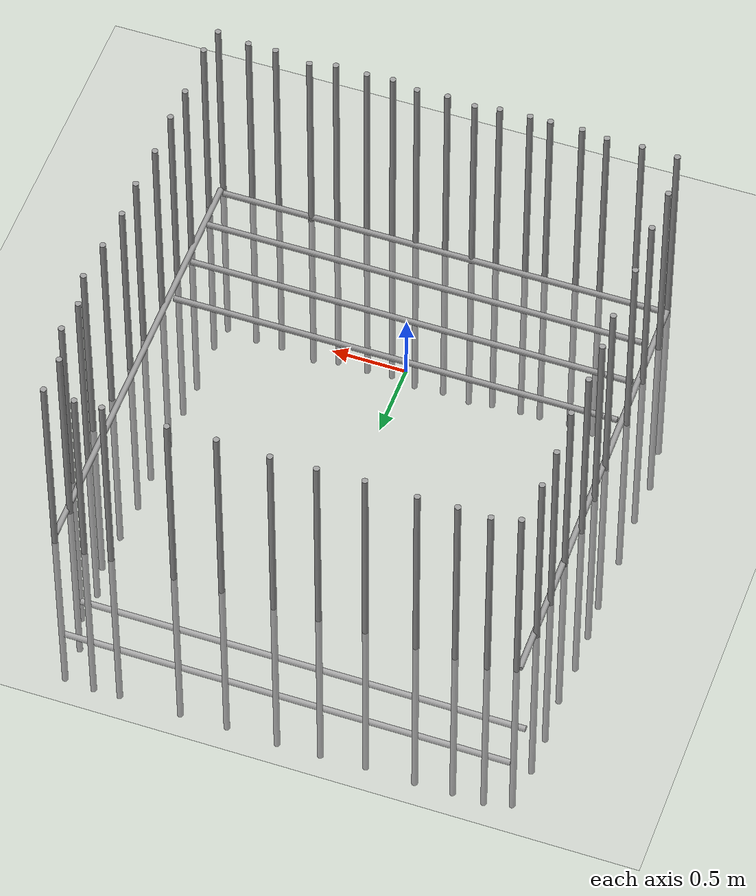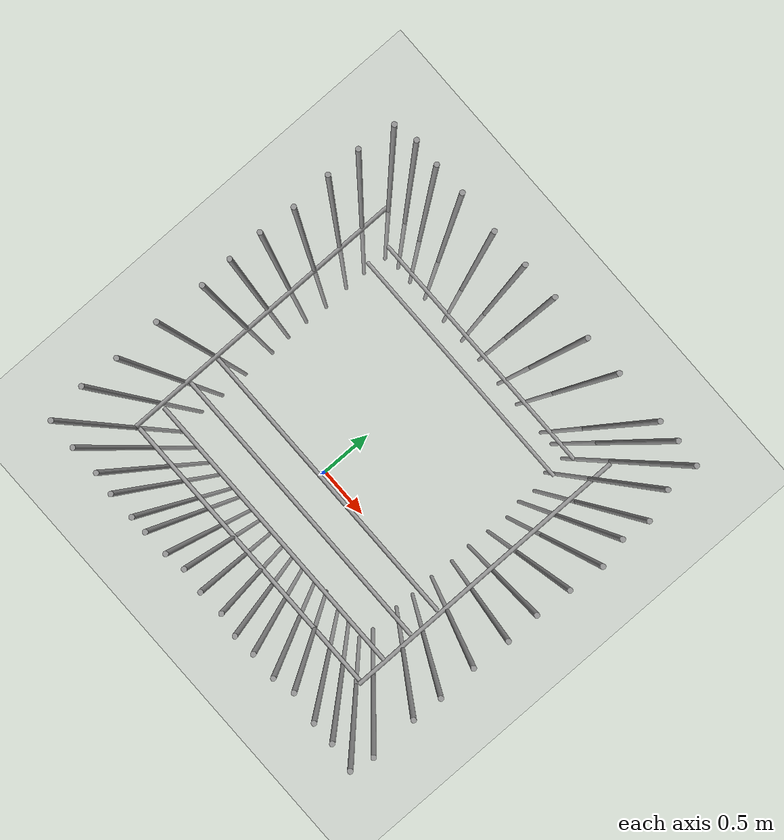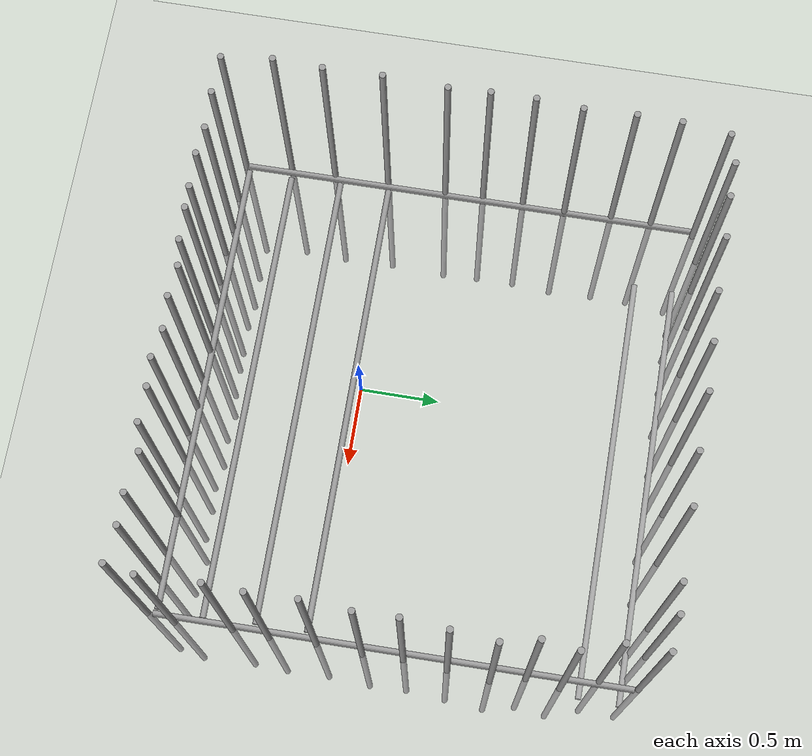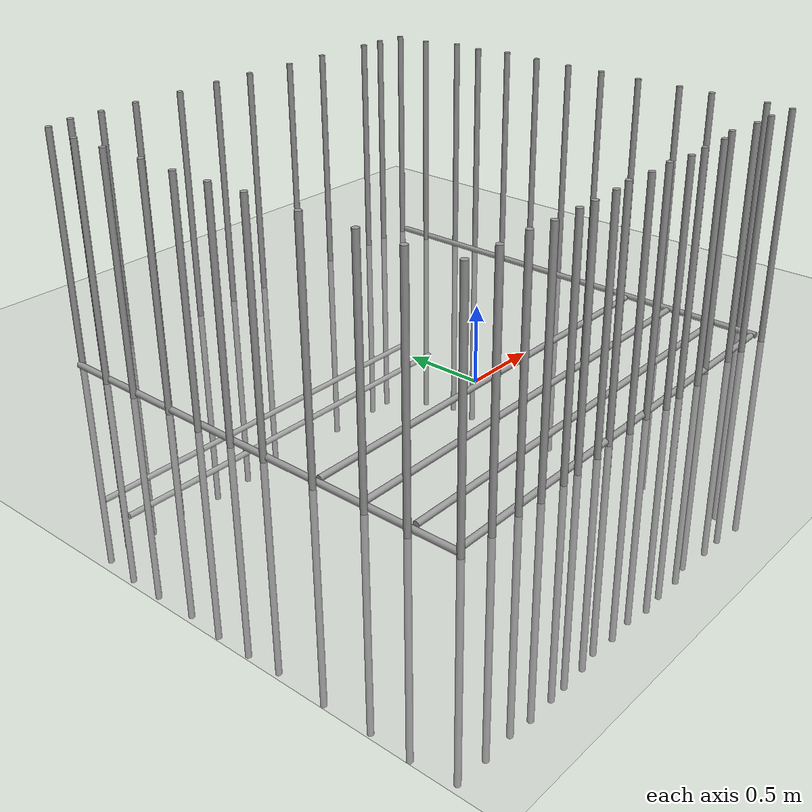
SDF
<sdf version="1.7">
 <world name="default">
  <light name="sun" type="directional">
   <pose>0 0 10 0 -0 0</pose>
   <diffuse>0.8 0.8 0.8 1</diffuse>
   <specular>0.2 0.2 0.2 1</specular>
   <attenuation>
    <range>1000</range>
    <constant>0.9</constant>
    <linear>0.01</linear>
    <quadratic>0.001</quadratic>
   </attenuation>
   <direction>-0.5 0.1 -0.9</direction>
   <spot><inner_angle>0</inner_angle><outer_angle>0</outer_angle><falloff>0</falloff></spot>
  </light>
  <model name="ground_plane">
   <static>1</static>
   <link name="link">
    <collision name="collision">
     <geometry><plane><normal>0 0 1</normal><size>100 100</size></plane></geometry>
     <surface><friction><ode><mu>100</mu><mu2>50</mu2></ode></friction></surface>
    </collision>
    <visual name="visual">
     <cast_shadows>0</cast_shadows>
     <geometry><plane><normal>0 0 1</normal><size>100 100</size></plane></geometry>
     <material>
      <texture><uri>file:/home/ronin/ws_smart_car/src/world_pkg/world/ground_plane.png</uri></texture>
     </material>
    </visual>
   </link>
  </model>
  <gravity>0 0 -9.8</gravity>
  <magnetic_field>6e-06 2.3e-05 -4.2e-05</magnetic_field>
  <atmosphere type="adiabatic"/>
  <physics type="ode">
   <max_step_size>0.001</max_step_size>
   <real_time_factor>1</real_time_factor>
   <real_time_update_rate>1000</real_time_update_rate>
  </physics>
  <scene><ambient>0.4 0.4 0.4 1</ambient><background>0.7 0.7 0.7 1</background><shadows>1</shadows></scene>
  <audio><device>default</device></audio>
  <spherical_coordinates>
   <surface_model>EARTH_WGS84</surface_model>
   <latitude_deg>0</latitude_deg>
   <longitude_deg>0</longitude_deg>
   <elevation>0</elevation>
   <heading_deg>0</heading_deg>
  </spherical_coordinates>
  <model name="Rebar">
   <static>1</static>
   <link name="link_0">
    <inertial>
     <mass>1</mass>
     <inertia><ixx>0.145833</ixx><ixy>0</ixy><ixz>0</ixz><iyy>0.145833</iyy><iyz>0</iyz><izz>0.125</izz></inertia>
    </inertial>
    <pose>0 0 -0 0 1.57 0</pose>
    <visual name="visual">
     <geometry><cylinder><radius>0.02</radius><length>3</length></cylinder></geometry>
     <material>
      <lighting>1</lighting>
      <script><uri>file://media/materials/scripts/gazebo.material</uri><name>Gazebo/Grey</name></script>
      <shader type="pixel"><normal_map>__default__</normal_map></shader>
      <ambient>0.3 0.3 0.3 1</ambient>
      <diffuse>0.7 0.7 0.7 1</diffuse>
      <specular>0.01 0.01 0.01 1</specular>
      <emissive>0 0 0 1</emissive>
     </material>
    </visual>
    <collision name="collision">
     <geometry><cylinder><radius>0.02</radius><length>3</length></cylinder></geometry>
     <surface>
      <friction>
       <ode><mu>1</mu><mu2>1</mu2><fdir1>0 0 0</fdir1><slip1>0</slip1><slip2>0</slip2></ode>
       <torsional>
        <coefficient>1</coefficient>
        <patch_radius>0</patch_radius>
        <surface_radius>0</surface_radius>
        <use_patch_radius>1</use_patch_radius>
        <ode><slip>0</slip></ode>
       </torsional>
      </friction>
      <bounce><restitution_coefficient>0</restitution_coefficient><threshold>1e+06</threshold></bounce>
      <contact>
       <collide_without_contact>0</collide_without_contact>
       <collide_without_contact_bitmask>1</collide_without_contact_bitmask>
       <collide_bitmask>1</collide_bitmask>
       <ode>
        <soft_cfm>0</soft_cfm>
        <soft_erp>0.2</soft_erp>
        <kp>1e+13</kp>
        <kd>1</kd>
        <max_vel>0.01</max_vel>
        <min_depth>0</min_depth>
       </ode>
       <bullet>
        <split_impulse>1</split_impulse>
        <split_impulse_penetration_threshold>-0.01</split_impulse_penetration_threshold>
        <soft_cfm>0</soft_cfm>
        <soft_erp>0.2</soft_erp>
        <kp>1e+13</kp>
        <kd>1</kd>
       </bullet>
      </contact>
     </surface>
    </collision>
   </link>
   <static>0</static>
   <pose>0.110276 -0.999396 0.019459 3.8e-05 0.001161 -0</pose>
  </model>
  <model name="Rebar_clone">
   <link name="link_0">
    <inertial>
     <mass>1</mass>
     <inertia><ixx>0.145833</ixx><ixy>0</ixy><ixz>0</ixz><iyy>0.145833</iyy><iyz>0</iyz><izz>0.125</izz></inertia>
    </inertial>
    <pose>0 0 -0 0 1.57 0</pose>
    <visual name="visual">
     <geometry><cylinder><radius>0.02</radius><length>3</length></cylinder></geometry>
     <material>
      <lighting>1</lighting>
      <script><uri>file://media/materials/scripts/gazebo.material</uri><name>Gazebo/Grey</name></script>
      <shader type="pixel"><normal_map>__default__</normal_map></shader>
      <ambient>0.3 0.3 0.3 1</ambient>
      <diffuse>0.7 0.7 0.7 1</diffuse>
      <specular>0.01 0.01 0.01 1</specular>
      <emissive>0 0 0 1</emissive>
     </material>
    </visual>
    <collision name="collision">
     <geometry><cylinder><radius>0.02</radius><length>3</length></cylinder></geometry>
     <surface>
      <friction>
       <ode><mu>1</mu><mu2>1</mu2><fdir1>0 0 0</fdir1><slip1>0</slip1><slip2>0</slip2></ode>
       <torsional>
        <coefficient>1</coefficient>
        <patch_radius>0</patch_radius>
        <surface_radius>0</surface_radius>
        <use_patch_radius>1</use_patch_radius>
        <ode><slip>0</slip></ode>
       </torsional>
      </friction>
      <bounce><restitution_coefficient>0</restitution_coefficient><threshold>1e+06</threshold></bounce>
      <contact>
       <collide_without_contact>0</collide_without_contact>
       <collide_without_contact_bitmask>1</collide_without_contact_bitmask>
       <collide_bitmask>1</collide_bitmask>
       <ode>
        <soft_cfm>0</soft_cfm>
        <soft_erp>0.2</soft_erp>
        <kp>1e+13</kp>
        <kd>1</kd>
        <max_vel>0.01</max_vel>
        <min_depth>0</min_depth>
       </ode>
       <bullet>
        <split_impulse>1</split_impulse>
        <split_impulse_penetration_threshold>-0.01</split_impulse_penetration_threshold>
        <soft_cfm>0</soft_cfm>
        <soft_erp>0.2</soft_erp>
        <kp>1e+13</kp>
        <kd>1</kd>
       </bullet>
      </contact>
     </surface>
    </collision>
   </link>
   <static>0</static>
   <pose>0.117632 -0.713055 0.019459 0.000487 0.000436 -1.1e-05</pose>
  </model>
  <model name="Rebar_clone_0">
   <static>1</static>
   <link name="link_0">
    <inertial>
     <mass>1</mass>
     <inertia><ixx>0.145833</ixx><ixy>0</ixy><ixz>0</ixz><iyy>0.145833</iyy><iyz>0</iyz><izz>0.125</izz></inertia>
    </inertial>
    <pose>0 0 -0 0 1.57 0</pose>
    <visual name="visual">
     <geometry><cylinder><radius>0.02</radius><length>3</length></cylinder></geometry>
     <material>
      <lighting>1</lighting>
      <script><uri>file://media/materials/scripts/gazebo.material</uri><name>Gazebo/Grey</name></script>
      <shader type="pixel"><normal_map>__default__</normal_map></shader>
      <ambient>0.3 0.3 0.3 1</ambient>
      <diffuse>0.7 0.7 0.7 1</diffuse>
      <specular>0.01 0.01 0.01 1</specular>
      <emissive>0 0 0 1</emissive>
     </material>
    </visual>
    <collision name="collision">
     <geometry><cylinder><radius>0.02</radius><length>3</length></cylinder></geometry>
     <surface>
      <friction>
       <ode><mu>1</mu><mu2>1</mu2><fdir1>0 0 0</fdir1><slip1>0</slip1><slip2>0</slip2></ode>
       <torsional>
        <coefficient>1</coefficient>
        <patch_radius>0</patch_radius>
        <surface_radius>0</surface_radius>
        <use_patch_radius>1</use_patch_radius>
        <ode><slip>0</slip></ode>
       </torsional>
      </friction>
      <bounce><restitution_coefficient>0</restitution_coefficient><threshold>1e+06</threshold></bounce>
      <contact>
       <collide_without_contact>0</collide_without_contact>
       <collide_without_contact_bitmask>1</collide_without_contact_bitmask>
       <collide_bitmask>1</collide_bitmask>
       <ode>
        <soft_cfm>0</soft_cfm>
        <soft_erp>0.2</soft_erp>
        <kp>1e+13</kp>
        <kd>1</kd>
        <max_vel>0.01</max_vel>
        <min_depth>0</min_depth>
       </ode>
       <bullet>
        <split_impulse>1</split_impulse>
        <split_impulse_penetration_threshold>-0.01</split_impulse_penetration_threshold>
        <soft_cfm>0</soft_cfm>
        <soft_erp>0.2</soft_erp>
        <kp>1e+13</kp>
        <kd>1</kd>
       </bullet>
      </contact>
     </surface>
    </collision>
   </link>
   <static>0</static>
   <pose>0.105314 -0.383399 0.019459 0 0.001153 0</pose>
  </model>
  <model name="Rebar_cross">
   <static>1</static>
   <link name="link_0">
    <inertial>
     <mass>1</mass>
     <inertia><ixx>0.145833</ixx><ixy>0</ixy><ixz>0</ixz><iyy>0.145833</iyy><iyz>0</iyz><izz>0.125</izz></inertia>
    </inertial>
    <pose>0 0 0 1.57002 1.57 2.4e-05</pose>
    <visual name="visual">
     <geometry><cylinder><radius>0.02</radius><length>3</length></cylinder></geometry>
     <material>
      <lighting>1</lighting>
      <script><uri>file://media/materials/scripts/gazebo.material</uri><name>Gazebo/Grey</name></script>
      <shader type="pixel"><normal_map>__default__</normal_map></shader>
      <ambient>0.3 0.3 0.3 1</ambient>
      <diffuse>0.7 0.7 0.7 1</diffuse>
      <specular>0.01 0.01 0.01 1</specular>
      <emissive>0 0 0 1</emissive>
     </material>
    </visual>
    <collision name="collision">
     <geometry><cylinder><radius>0.02</radius><length>3</length></cylinder></geometry>
     <surface>
      <friction>
       <ode><mu>1</mu><mu2>1</mu2><fdir1>0 0 0</fdir1><slip1>0</slip1><slip2>0</slip2></ode>
       <torsional>
        <coefficient>1</coefficient>
        <patch_radius>0</patch_radius>
        <surface_radius>0</surface_radius>
        <use_patch_radius>1</use_patch_radius>
        <ode><slip>0</slip></ode>
       </torsional>
      </friction>
      <bounce><restitution_coefficient>0</restitution_coefficient><threshold>1e+06</threshold></bounce>
      <contact>
       <collide_without_contact>0</collide_without_contact>
       <collide_without_contact_bitmask>1</collide_without_contact_bitmask>
       <collide_bitmask>1</collide_bitmask>
       <ode>
        <soft_cfm>0</soft_cfm>
        <soft_erp>0.2</soft_erp>
        <kp>1e+13</kp>
        <kd>1</kd>
        <max_vel>0.01</max_vel>
        <min_depth>0</min_depth>
       </ode>
       <bullet>
        <split_impulse>1</split_impulse>
        <split_impulse_penetration_threshold>-0.01</split_impulse_penetration_threshold>
        <soft_cfm>0</soft_cfm>
        <soft_erp>0.2</soft_erp>
        <kp>1e+13</kp>
        <kd>1</kd>
       </bullet>
      </contact>
     </surface>
    </collision>
   </link>
   <static>0</static>
   <pose>-1.42412 0.482138 0.02 1e-06 -0 -4e-06</pose>
  </model>
  <model name="Rebar_cross_clone">
   <static>1</static>
   <link name="link_0">
    <inertial>
     <mass>1</mass>
     <inertia><ixx>0.145833</ixx><ixy>0</ixy><ixz>0</ixz><iyy>0.145833</iyy><iyz>0</iyz><izz>0.125</izz></inertia>
    </inertial>
    <pose>0 0 0 1.57002 1.57 2.4e-05</pose>
    <visual name="visual">
     <geometry><cylinder><radius>0.02</radius><length>3</length></cylinder></geometry>
     <material>
      <lighting>1</lighting>
      <script><uri>file://media/materials/scripts/gazebo.material</uri><name>Gazebo/Grey</name></script>
      <shader type="pixel"><normal_map>__default__</normal_map></shader>
      <ambient>0.3 0.3 0.3 1</ambient>
      <diffuse>0.7 0.7 0.7 1</diffuse>
      <specular>0.01 0.01 0.01 1</specular>
      <emissive>0 0 0 1</emissive>
     </material>
    </visual>
    <collision name="collision">
     <geometry><cylinder><radius>0.02</radius><length>3</length></cylinder></geometry>
     <surface>
      <friction>
       <ode><mu>1</mu><mu2>1</mu2><fdir1>0 0 0</fdir1><slip1>0</slip1><slip2>0</slip2></ode>
       <torsional>
        <coefficient>1</coefficient>
        <patch_radius>0</patch_radius>
        <surface_radius>0</surface_radius>
        <use_patch_radius>1</use_patch_radius>
        <ode><slip>0</slip></ode>
       </torsional>
      </friction>
      <bounce><restitution_coefficient>0</restitution_coefficient><threshold>1e+06</threshold></bounce>
      <contact>
       <collide_without_contact>0</collide_without_contact>
       <collide_without_contact_bitmask>1</collide_without_contact_bitmask>
       <collide_bitmask>1</collide_bitmask>
       <ode>
        <soft_cfm>0</soft_cfm>
        <soft_erp>0.2</soft_erp>
        <kp>1e+13</kp>
        <kd>1</kd>
        <max_vel>0.01</max_vel>
        <min_depth>0</min_depth>
       </ode>
       <bullet>
        <split_impulse>1</split_impulse>
        <split_impulse_penetration_threshold>-0.01</split_impulse_penetration_threshold>
        <soft_cfm>0</soft_cfm>
        <soft_erp>0.2</soft_erp>
        <kp>1e+13</kp>
        <kd>1</kd>
       </bullet>
      </contact>
     </surface>
    </collision>
   </link>
   <static>0</static>
   <pose>1.63477 0.477366 0.02 -3e-06 0.003983 0.001736</pose>
  </model>
  <model name="Rebar_clone_0_clone">
   <static>1</static>
   <link name="link_0">
    <inertial>
     <mass>1</mass>
     <inertia><ixx>0.145833</ixx><ixy>0</ixy><ixz>0</ixz><iyy>0.145833</iyy><iyz>0</iyz><izz>0.125</izz></inertia>
    </inertial>
    <pose>0 0 -0 0 1.57 0</pose>
    <visual name="visual">
     <geometry><cylinder><radius>0.02</radius><length>3</length></cylinder></geometry>
     <material>
      <lighting>1</lighting>
      <script><uri>file://media/materials/scripts/gazebo.material</uri><name>Gazebo/Grey</name></script>
      <shader type="pixel"><normal_map>__default__</normal_map></shader>
      <ambient>0.3 0.3 0.3 1</ambient>
      <diffuse>0.7 0.7 0.7 1</diffuse>
      <specular>0.01 0.01 0.01 1</specular>
      <emissive>0 0 0 1</emissive>
     </material>
    </visual>
    <collision name="collision">
     <geometry><cylinder><radius>0.02</radius><length>3</length></cylinder></geometry>
     <surface>
      <friction>
       <ode><mu>1</mu><mu2>1</mu2><fdir1>0 0 0</fdir1><slip1>0</slip1><slip2>0</slip2></ode>
       <torsional>
        <coefficient>1</coefficient>
        <patch_radius>0</patch_radius>
        <surface_radius>0</surface_radius>
        <use_patch_radius>1</use_patch_radius>
        <ode><slip>0</slip></ode>
       </torsional>
      </friction>
      <bounce><restitution_coefficient>0</restitution_coefficient><threshold>1e+06</threshold></bounce>
      <contact>
       <collide_without_contact>0</collide_without_contact>
       <collide_without_contact_bitmask>1</collide_without_contact_bitmask>
       <collide_bitmask>1</collide_bitmask>
       <ode>
        <soft_cfm>0</soft_cfm>
        <soft_erp>0.2</soft_erp>
        <kp>1e+13</kp>
        <kd>1</kd>
        <max_vel>0.01</max_vel>
        <min_depth>0</min_depth>
       </ode>
       <bullet>
        <split_impulse>1</split_impulse>
        <split_impulse_penetration_threshold>-0.01</split_impulse_penetration_threshold>
        <soft_cfm>0</soft_cfm>
        <soft_erp>0.2</soft_erp>
        <kp>1e+13</kp>
        <kd>1</kd>
       </bullet>
      </contact>
     </surface>
    </collision>
   </link>
   <static>0</static>
   <pose>0.102907 -0.059179 0.019459 0 0.001153 0</pose>
  </model>
  <model name="Rebar_clone_0_clone_5">
   <static>1</static>
   <link name="link_0">
    <inertial>
     <mass>1</mass>
     <inertia><ixx>0.145833</ixx><ixy>0</ixy><ixz>0</ixz><iyy>0.145833</iyy><iyz>0</iyz><izz>0.125</izz></inertia>
    </inertial>
    <pose>0 0 -0 0 1.57 0</pose>
    <visual name="visual">
     <geometry><cylinder><radius>0.02</radius><length>3</length></cylinder></geometry>
     <material>
      <lighting>1</lighting>
      <script><uri>file://media/materials/scripts/gazebo.material</uri><name>Gazebo/Grey</name></script>
      <shader type="pixel"><normal_map>__default__</normal_map></shader>
      <ambient>0.3 0.3 0.3 1</ambient>
      <diffuse>0.7 0.7 0.7 1</diffuse>
      <specular>0.01 0.01 0.01 1</specular>
      <emissive>0 0 0 1</emissive>
     </material>
    </visual>
    <collision name="collision">
     <geometry><cylinder><radius>0.02</radius><length>3</length></cylinder></geometry>
     <surface>
      <friction>
       <ode><mu>1</mu><mu2>1</mu2><fdir1>0 0 0</fdir1><slip1>0</slip1><slip2>0</slip2></ode>
       <torsional>
        <coefficient>1</coefficient>
        <patch_radius>0</patch_radius>
        <surface_radius>0</surface_radius>
        <use_patch_radius>1</use_patch_radius>
        <ode><slip>0</slip></ode>
       </torsional>
      </friction>
      <bounce><restitution_coefficient>0</restitution_coefficient><threshold>1e+06</threshold></bounce>
      <contact>
       <collide_without_contact>0</collide_without_contact>
       <collide_without_contact_bitmask>1</collide_without_contact_bitmask>
       <collide_bitmask>1</collide_bitmask>
       <ode>
        <soft_cfm>0</soft_cfm>
        <soft_erp>0.2</soft_erp>
        <kp>1e+13</kp>
        <kd>1</kd>
        <max_vel>0.01</max_vel>
        <min_depth>0</min_depth>
       </ode>
       <bullet>
        <split_impulse>1</split_impulse>
        <split_impulse_penetration_threshold>-0.01</split_impulse_penetration_threshold>
        <soft_cfm>0</soft_cfm>
        <soft_erp>0.2</soft_erp>
        <kp>1e+13</kp>
        <kd>1</kd>
       </bullet>
      </contact>
     </surface>
    </collision>
   </link>
   <static>0</static>
   <pose>0.100655 1.71148 -1 0 0.001152 0</pose>
  </model>
  <model name="Rebar_clone_0_clone_6">
   <static>1</static>
   <link name="link_0">
    <inertial>
     <mass>1</mass>
     <inertia><ixx>0.145833</ixx><ixy>0</ixy><ixz>0</ixz><iyy>0.145833</iyy><iyz>0</iyz><izz>0.125</izz></inertia>
    </inertial>
    <pose>0 0 -0 0 1.57 0</pose>
    <visual name="visual">
     <geometry><cylinder><radius>0.02</radius><length>3</length></cylinder></geometry>
     <material>
      <lighting>1</lighting>
      <script><uri>file://media/materials/scripts/gazebo.material</uri><name>Gazebo/Grey</name></script>
      <shader type="pixel"><normal_map>__default__</normal_map></shader>
      <ambient>0.3 0.3 0.3 1</ambient>
      <diffuse>0.7 0.7 0.7 1</diffuse>
      <specular>0.01 0.01 0.01 1</specular>
      <emissive>0 0 0 1</emissive>
     </material>
    </visual>
    <collision name="collision">
     <geometry><cylinder><radius>0.02</radius><length>3</length></cylinder></geometry>
     <surface>
      <friction>
       <ode><mu>1</mu><mu2>1</mu2><fdir1>0 0 0</fdir1><slip1>0</slip1><slip2>0</slip2></ode>
       <torsional>
        <coefficient>1</coefficient>
        <patch_radius>0</patch_radius>
        <surface_radius>0</surface_radius>
        <use_patch_radius>1</use_patch_radius>
        <ode><slip>0</slip></ode>
       </torsional>
      </friction>
      <bounce><restitution_coefficient>0</restitution_coefficient><threshold>1e+06</threshold></bounce>
      <contact>
       <collide_without_contact>0</collide_without_contact>
       <collide_without_contact_bitmask>1</collide_without_contact_bitmask>
       <collide_bitmask>1</collide_bitmask>
       <ode>
        <soft_cfm>0</soft_cfm>
        <soft_erp>0.2</soft_erp>
        <kp>1e+13</kp>
        <kd>1</kd>
        <max_vel>0.01</max_vel>
        <min_depth>0</min_depth>
       </ode>
       <bullet>
        <split_impulse>1</split_impulse>
        <split_impulse_penetration_threshold>-0.01</split_impulse_penetration_threshold>
        <soft_cfm>0</soft_cfm>
        <soft_erp>0.2</soft_erp>
        <kp>1e+13</kp>
        <kd>1</kd>
       </bullet>
      </contact>
     </surface>
    </collision>
   </link>
   <static>0</static>
   <pose>0.110845 1.98674 -1 -0.001566 0.000435 0.00098</pose>
  </model>
  <model name="Rebar_vertial">
   <static>1</static>
   <link name="link_0">
    <inertial>
     <mass>1</mass>
     <inertia><ixx>0.145833</ixx><ixy>0</ixy><ixz>0</ixz><iyy>0.145833</iyy><iyz>0</iyz><izz>0.125</izz></inertia>
    </inertial>
    <visual name="visual">
     <geometry><cylinder><radius>0.02</radius><length>3</length></cylinder></geometry>
     <material>
      <lighting>1</lighting>
      <script><uri>file://media/materials/scripts/gazebo.material</uri><name>Gazebo/Grey</name></script>
      <shader type="pixel"><normal_map>__default__</normal_map></shader>
      <ambient>0.3 0.3 0.3 1</ambient>
      <diffuse>0.7 0.7 0.7 1</diffuse>
      <specular>0.01 0.01 0.01 1</specular>
      <emissive>0 0 0 1</emissive>
     </material>
    </visual>
    <collision name="collision">
     <geometry><cylinder><radius>0.02</radius><length>3</length></cylinder></geometry>
     <surface>
      <friction>
       <ode><mu>1</mu><mu2>1</mu2><fdir1>0 0 0</fdir1><slip1>0</slip1><slip2>0</slip2></ode>
       <torsional>
        <coefficient>1</coefficient>
        <patch_radius>0</patch_radius>
        <surface_radius>0</surface_radius>
        <use_patch_radius>1</use_patch_radius>
        <ode><slip>0</slip></ode>
       </torsional>
      </friction>
      <bounce><restitution_coefficient>0</restitution_coefficient><threshold>1e+06</threshold></bounce>
      <contact>
       <collide_without_contact>0</collide_without_contact>
       <collide_without_contact_bitmask>1</collide_without_contact_bitmask>
       <collide_bitmask>1</collide_bitmask>
       <ode>
        <soft_cfm>0</soft_cfm>
        <soft_erp>0.2</soft_erp>
        <kp>1e+13</kp>
        <kd>1</kd>
        <max_vel>0.01</max_vel>
        <min_depth>0</min_depth>
       </ode>
       <bullet>
        <split_impulse>1</split_impulse>
        <split_impulse_penetration_threshold>-0.01</split_impulse_penetration_threshold>
        <soft_cfm>0</soft_cfm>
        <soft_erp>0.2</soft_erp>
        <kp>1e+13</kp>
        <kd>1</kd>
       </bullet>
      </contact>
     </surface>
    </collision>
   </link>
   <static>0</static>
   <pose>1.6202 2.00322 0.019459 -0.001562 0.001157 0.000983</pose>
  </model>
  <model name="Rebar_vertial_clone">
   <static>1</static>
   <link name="link_0">
    <inertial>
     <mass>1</mass>
     <inertia><ixx>0.145833</ixx><ixy>0</ixy><ixz>0</ixz><iyy>0.145833</iyy><iyz>0</iyz><izz>0.125</izz></inertia>
    </inertial>
    <visual name="visual">
     <geometry><cylinder><radius>0.02</radius><length>3</length></cylinder></geometry>
     <material>
      <lighting>1</lighting>
      <script><uri>file://media/materials/scripts/gazebo.material</uri><name>Gazebo/Grey</name></script>
      <shader type="pixel"><normal_map>__default__</normal_map></shader>
      <ambient>0.3 0.3 0.3 1</ambient>
      <diffuse>0.7 0.7 0.7 1</diffuse>
      <specular>0.01 0.01 0.01 1</specular>
      <emissive>0 0 0 1</emissive>
     </material>
    </visual>
    <collision name="collision">
     <geometry><cylinder><radius>0.02</radius><length>3</length></cylinder></geometry>
     <surface>
      <friction>
       <ode><mu>1</mu><mu2>1</mu2><fdir1>0 0 0</fdir1><slip1>0</slip1><slip2>0</slip2></ode>
       <torsional>
        <coefficient>1</coefficient>
        <patch_radius>0</patch_radius>
        <surface_radius>0</surface_radius>
        <use_patch_radius>1</use_patch_radius>
        <ode><slip>0</slip></ode>
       </torsional>
      </friction>
      <bounce><restitution_coefficient>0</restitution_coefficient><threshold>1e+06</threshold></bounce>
      <contact>
       <collide_without_contact>0</collide_without_contact>
       <collide_without_contact_bitmask>1</collide_without_contact_bitmask>
       <collide_bitmask>1</collide_bitmask>
       <ode>
        <soft_cfm>0</soft_cfm>
        <soft_erp>0.2</soft_erp>
        <kp>1e+13</kp>
        <kd>1</kd>
        <max_vel>0.01</max_vel>
        <min_depth>0</min_depth>
       </ode>
       <bullet>
        <split_impulse>1</split_impulse>
        <split_impulse_penetration_threshold>-0.01</split_impulse_penetration_threshold>
        <soft_cfm>0</soft_cfm>
        <soft_erp>0.2</soft_erp>
        <kp>1e+13</kp>
        <kd>1</kd>
       </bullet>
      </contact>
     </surface>
    </collision>
   </link>
   <static>0</static>
   <pose>1.61527 1.75563 0.019459 -0.001562 0.001157 0.000983</pose>
  </model>
  <model name="Rebar_vertial_clone_0">
   <static>1</static>
   <link name="link_0">
    <inertial>
     <mass>1</mass>
     <inertia><ixx>0.145833</ixx><ixy>0</ixy><ixz>0</ixz><iyy>0.145833</iyy><iyz>0</iyz><izz>0.125</izz></inertia>
    </inertial>
    <visual name="visual">
     <geometry><cylinder><radius>0.02</radius><length>3</length></cylinder></geometry>
     <material>
      <lighting>1</lighting>
      <script><uri>file://media/materials/scripts/gazebo.material</uri><name>Gazebo/Grey</name></script>
      <shader type="pixel"><normal_map>__default__</normal_map></shader>
      <ambient>0.3 0.3 0.3 1</ambient>
      <diffuse>0.7 0.7 0.7 1</diffuse>
      <specular>0.01 0.01 0.01 1</specular>
      <emissive>0 0 0 1</emissive>
     </material>
    </visual>
    <collision name="collision">
     <geometry><cylinder><radius>0.02</radius><length>3</length></cylinder></geometry>
     <surface>
      <friction>
       <ode><mu>1</mu><mu2>1</mu2><fdir1>0 0 0</fdir1><slip1>0</slip1><slip2>0</slip2></ode>
       <torsional>
        <coefficient>1</coefficient>
        <patch_radius>0</patch_radius>
        <surface_radius>0</surface_radius>
        <use_patch_radius>1</use_patch_radius>
        <ode><slip>0</slip></ode>
       </torsional>
      </friction>
      <bounce><restitution_coefficient>0</restitution_coefficient><threshold>1e+06</threshold></bounce>
      <contact>
       <collide_without_contact>0</collide_without_contact>
       <collide_without_contact_bitmask>1</collide_without_contact_bitmask>
       <collide_bitmask>1</collide_bitmask>
       <ode>
        <soft_cfm>0</soft_cfm>
        <soft_erp>0.2</soft_erp>
        <kp>1e+13</kp>
        <kd>1</kd>
        <max_vel>0.01</max_vel>
        <min_depth>0</min_depth>
       </ode>
       <bullet>
        <split_impulse>1</split_impulse>
        <split_impulse_penetration_threshold>-0.01</split_impulse_penetration_threshold>
        <soft_cfm>0</soft_cfm>
        <soft_erp>0.2</soft_erp>
        <kp>1e+13</kp>
        <kd>1</kd>
       </bullet>
      </contact>
     </surface>
    </collision>
   </link>
   <static>0</static>
   <pose>1.69097 1.52613 0.019459 -0.001562 0.001157 0.000983</pose>
  </model>
  <model name="Rebar_vertial_clone_1">
   <static>1</static>
   <link name="link_0">
    <inertial>
     <mass>1</mass>
     <inertia><ixx>0.145833</ixx><ixy>0</ixy><ixz>0</ixz><iyy>0.145833</iyy><iyz>0</iyz><izz>0.125</izz></inertia>
    </inertial>
    <visual name="visual">
     <geometry><cylinder><radius>0.02</radius><length>3</length></cylinder></geometry>
     <material>
      <lighting>1</lighting>
      <script><uri>file://media/materials/scripts/gazebo.material</uri><name>Gazebo/Grey</name></script>
      <shader type="pixel"><normal_map>__default__</normal_map></shader>
      <ambient>0.3 0.3 0.3 1</ambient>
      <diffuse>0.7 0.7 0.7 1</diffuse>
      <specular>0.01 0.01 0.01 1</specular>
      <emissive>0 0 0 1</emissive>
     </material>
    </visual>
    <collision name="collision">
     <geometry><cylinder><radius>0.02</radius><length>3</length></cylinder></geometry>
     <surface>
      <friction>
       <ode><mu>1</mu><mu2>1</mu2><fdir1>0 0 0</fdir1><slip1>0</slip1><slip2>0</slip2></ode>
       <torsional>
        <coefficient>1</coefficient>
        <patch_radius>0</patch_radius>
        <surface_radius>0</surface_radius>
        <use_patch_radius>1</use_patch_radius>
        <ode><slip>0</slip></ode>
       </torsional>
      </friction>
      <bounce><restitution_coefficient>0</restitution_coefficient><threshold>1e+06</threshold></bounce>
      <contact>
       <collide_without_contact>0</collide_without_contact>
       <collide_without_contact_bitmask>1</collide_without_contact_bitmask>
       <collide_bitmask>1</collide_bitmask>
       <ode>
        <soft_cfm>0</soft_cfm>
        <soft_erp>0.2</soft_erp>
        <kp>1e+13</kp>
        <kd>1</kd>
        <max_vel>0.01</max_vel>
        <min_depth>0</min_depth>
       </ode>
       <bullet>
        <split_impulse>1</split_impulse>
        <split_impulse_penetration_threshold>-0.01</split_impulse_penetration_threshold>
        <soft_cfm>0</soft_cfm>
        <soft_erp>0.2</soft_erp>
        <kp>1e+13</kp>
        <kd>1</kd>
       </bullet>
      </contact>
     </surface>
    </collision>
   </link>
   <static>0</static>
   <pose>1.66538 1.31262 0.019459 -0.001562 0.001157 0.000983</pose>
  </model>
  <model name="Rebar_vertial_clone_2">
   <static>1</static>
   <link name="link_0">
    <inertial>
     <mass>1</mass>
     <inertia><ixx>0.145833</ixx><ixy>0</ixy><ixz>0</ixz><iyy>0.145833</iyy><iyz>0</iyz><izz>0.125</izz></inertia>
    </inertial>
    <visual name="visual">
     <geometry><cylinder><radius>0.02</radius><length>3</length></cylinder></geometry>
     <material>
      <lighting>1</lighting>
      <script><uri>file://media/materials/scripts/gazebo.material</uri><name>Gazebo/Grey</name></script>
      <shader type="pixel"><normal_map>__default__</normal_map></shader>
      <ambient>0.3 0.3 0.3 1</ambient>
      <diffuse>0.7 0.7 0.7 1</diffuse>
      <specular>0.01 0.01 0.01 1</specular>
      <emissive>0 0 0 1</emissive>
     </material>
    </visual>
    <collision name="collision">
     <geometry><cylinder><radius>0.02</radius><length>3</length></cylinder></geometry>
     <surface>
      <friction>
       <ode><mu>1</mu><mu2>1</mu2><fdir1>0 0 0</fdir1><slip1>0</slip1><slip2>0</slip2></ode>
       <torsional>
        <coefficient>1</coefficient>
        <patch_radius>0</patch_radius>
        <surface_radius>0</surface_radius>
        <use_patch_radius>1</use_patch_radius>
        <ode><slip>0</slip></ode>
       </torsional>
      </friction>
      <bounce><restitution_coefficient>0</restitution_coefficient><threshold>1e+06</threshold></bounce>
      <contact>
       <collide_without_contact>0</collide_without_contact>
       <collide_without_contact_bitmask>1</collide_without_contact_bitmask>
       <collide_bitmask>1</collide_bitmask>
       <ode>
        <soft_cfm>0</soft_cfm>
        <soft_erp>0.2</soft_erp>
        <kp>1e+13</kp>
        <kd>1</kd>
        <max_vel>0.01</max_vel>
        <min_depth>0</min_depth>
       </ode>
       <bullet>
        <split_impulse>1</split_impulse>
        <split_impulse_penetration_threshold>-0.01</split_impulse_penetration_threshold>
        <soft_cfm>0</soft_cfm>
        <soft_erp>0.2</soft_erp>
        <kp>1e+13</kp>
        <kd>1</kd>
       </bullet>
      </contact>
     </surface>
    </collision>
   </link>
   <static>0</static>
   <pose>1.71531 1.09533 0.019459 -0.001562 0.001157 0.000983</pose>
  </model>
  <model name="Rebar_vertial_clone_3">
   <static>1</static>
   <link name="link_0">
    <inertial>
     <mass>1</mass>
     <inertia><ixx>0.145833</ixx><ixy>0</ixy><ixz>0</ixz><iyy>0.145833</iyy><iyz>0</iyz><izz>0.125</izz></inertia>
    </inertial>
    <visual name="visual">
     <geometry><cylinder><radius>0.02</radius><length>3</length></cylinder></geometry>
     <material>
      <lighting>1</lighting>
      <script><uri>file://media/materials/scripts/gazebo.material</uri><name>Gazebo/Grey</name></script>
      <shader type="pixel"><normal_map>__default__</normal_map></shader>
      <ambient>0.3 0.3 0.3 1</ambient>
      <diffuse>0.7 0.7 0.7 1</diffuse>
      <specular>0.01 0.01 0.01 1</specular>
      <emissive>0 0 0 1</emissive>
     </material>
    </visual>
    <collision name="collision">
     <geometry><cylinder><radius>0.02</radius><length>3</length></cylinder></geometry>
     <surface>
      <friction>
       <ode><mu>1</mu><mu2>1</mu2><fdir1>0 0 0</fdir1><slip1>0</slip1><slip2>0</slip2></ode>
       <torsional>
        <coefficient>1</coefficient>
        <patch_radius>0</patch_radius>
        <surface_radius>0</surface_radius>
        <use_patch_radius>1</use_patch_radius>
        <ode><slip>0</slip></ode>
       </torsional>
      </friction>
      <bounce><restitution_coefficient>0</restitution_coefficient><threshold>1e+06</threshold></bounce>
      <contact>
       <collide_without_contact>0</collide_without_contact>
       <collide_without_contact_bitmask>1</collide_without_contact_bitmask>
       <collide_bitmask>1</collide_bitmask>
       <ode>
        <soft_cfm>0</soft_cfm>
        <soft_erp>0.2</soft_erp>
        <kp>1e+13</kp>
        <kd>1</kd>
        <max_vel>0.01</max_vel>
        <min_depth>0</min_depth>
       </ode>
       <bullet>
        <split_impulse>1</split_impulse>
        <split_impulse_penetration_threshold>-0.01</split_impulse_penetration_threshold>
        <soft_cfm>0</soft_cfm>
        <soft_erp>0.2</soft_erp>
        <kp>1e+13</kp>
        <kd>1</kd>
       </bullet>
      </contact>
     </surface>
    </collision>
   </link>
   <static>0</static>
   <pose>1.69149 0.827238 0.019459 -0.001562 0.001157 0.000983</pose>
  </model>
  <model name="Rebar_vertial_clone_4">
   <static>1</static>
   <link name="link_0">
    <inertial>
     <mass>1</mass>
     <inertia><ixx>0.145833</ixx><ixy>0</ixy><ixz>0</ixz><iyy>0.145833</iyy><iyz>0</iyz><izz>0.125</izz></inertia>
    </inertial>
    <visual name="visual">
     <geometry><cylinder><radius>0.02</radius><length>3</length></cylinder></geometry>
     <material>
      <lighting>1</lighting>
      <script><uri>file://media/materials/scripts/gazebo.material</uri><name>Gazebo/Grey</name></script>
      <shader type="pixel"><normal_map>__default__</normal_map></shader>
      <ambient>0.3 0.3 0.3 1</ambient>
      <diffuse>0.7 0.7 0.7 1</diffuse>
      <specular>0.01 0.01 0.01 1</specular>
      <emissive>0 0 0 1</emissive>
     </material>
    </visual>
    <collision name="collision">
     <geometry><cylinder><radius>0.02</radius><length>3</length></cylinder></geometry>
     <surface>
      <friction>
       <ode><mu>1</mu><mu2>1</mu2><fdir1>0 0 0</fdir1><slip1>0</slip1><slip2>0</slip2></ode>
       <torsional>
        <coefficient>1</coefficient>
        <patch_radius>0</patch_radius>
        <surface_radius>0</surface_radius>
        <use_patch_radius>1</use_patch_radius>
        <ode><slip>0</slip></ode>
       </torsional>
      </friction>
      <bounce><restitution_coefficient>0</restitution_coefficient><threshold>1e+06</threshold></bounce>
      <contact>
       <collide_without_contact>0</collide_without_contact>
       <collide_without_contact_bitmask>1</collide_without_contact_bitmask>
       <collide_bitmask>1</collide_bitmask>
       <ode>
        <soft_cfm>0</soft_cfm>
        <soft_erp>0.2</soft_erp>
        <kp>1e+13</kp>
        <kd>1</kd>
        <max_vel>0.01</max_vel>
        <min_depth>0</min_depth>
       </ode>
       <bullet>
        <split_impulse>1</split_impulse>
        <split_impulse_penetration_threshold>-0.01</split_impulse_penetration_threshold>
        <soft_cfm>0</soft_cfm>
        <soft_erp>0.2</soft_erp>
        <kp>1e+13</kp>
        <kd>1</kd>
       </bullet>
      </contact>
     </surface>
    </collision>
   </link>
   <static>0</static>
   <pose>1.67107 0.552466 0.019459 -0.001562 0.001157 0.000983</pose>
  </model>
  <model name="Rebar_vertial_clone_5">
   <static>1</static>
   <link name="link_0">
    <inertial>
     <mass>1</mass>
     <inertia><ixx>0.145833</ixx><ixy>0</ixy><ixz>0</ixz><iyy>0.145833</iyy><iyz>0</iyz><izz>0.125</izz></inertia>
    </inertial>
    <visual name="visual">
     <geometry><cylinder><radius>0.02</radius><length>3</length></cylinder></geometry>
     <material>
      <lighting>1</lighting>
      <script><uri>file://media/materials/scripts/gazebo.material</uri><name>Gazebo/Grey</name></script>
      <shader type="pixel"><normal_map>__default__</normal_map></shader>
      <ambient>0.3 0.3 0.3 1</ambient>
      <diffuse>0.7 0.7 0.7 1</diffuse>
      <specular>0.01 0.01 0.01 1</specular>
      <emissive>0 0 0 1</emissive>
     </material>
    </visual>
    <collision name="collision">
     <geometry><cylinder><radius>0.02</radius><length>3</length></cylinder></geometry>
     <surface>
      <friction>
       <ode><mu>1</mu><mu2>1</mu2><fdir1>0 0 0</fdir1><slip1>0</slip1><slip2>0</slip2></ode>
       <torsional>
        <coefficient>1</coefficient>
        <patch_radius>0</patch_radius>
        <surface_radius>0</surface_radius>
        <use_patch_radius>1</use_patch_radius>
        <ode><slip>0</slip></ode>
       </torsional>
      </friction>
      <bounce><restitution_coefficient>0</restitution_coefficient><threshold>1e+06</threshold></bounce>
      <contact>
       <collide_without_contact>0</collide_without_contact>
       <collide_without_contact_bitmask>1</collide_without_contact_bitmask>
       <collide_bitmask>1</collide_bitmask>
       <ode>
        <soft_cfm>0</soft_cfm>
        <soft_erp>0.2</soft_erp>
        <kp>1e+13</kp>
        <kd>1</kd>
        <max_vel>0.01</max_vel>
        <min_depth>0</min_depth>
       </ode>
       <bullet>
        <split_impulse>1</split_impulse>
        <split_impulse_penetration_threshold>-0.01</split_impulse_penetration_threshold>
        <soft_cfm>0</soft_cfm>
        <soft_erp>0.2</soft_erp>
        <kp>1e+13</kp>
        <kd>1</kd>
       </bullet>
      </contact>
     </surface>
    </collision>
   </link>
   <static>0</static>
   <pose>1.67747 0.296676 0.019459 -0.001562 0.001157 0.000983</pose>
  </model>
  <model name="Rebar_vertial_clone_6">
   <static>1</static>
   <link name="link_0">
    <inertial>
     <mass>1</mass>
     <inertia><ixx>0.145833</ixx><ixy>0</ixy><ixz>0</ixz><iyy>0.145833</iyy><iyz>0</iyz><izz>0.125</izz></inertia>
    </inertial>
    <visual name="visual">
     <geometry><cylinder><radius>0.02</radius><length>3</length></cylinder></geometry>
     <material>
      <lighting>1</lighting>
      <script><uri>file://media/materials/scripts/gazebo.material</uri><name>Gazebo/Grey</name></script>
      <shader type="pixel"><normal_map>__default__</normal_map></shader>
      <ambient>0.3 0.3 0.3 1</ambient>
      <diffuse>0.7 0.7 0.7 1</diffuse>
      <specular>0.01 0.01 0.01 1</specular>
      <emissive>0 0 0 1</emissive>
     </material>
    </visual>
    <collision name="collision">
     <geometry><cylinder><radius>0.02</radius><length>3</length></cylinder></geometry>
     <surface>
      <friction>
       <ode><mu>1</mu><mu2>1</mu2><fdir1>0 0 0</fdir1><slip1>0</slip1><slip2>0</slip2></ode>
       <torsional>
        <coefficient>1</coefficient>
        <patch_radius>0</patch_radius>
        <surface_radius>0</surface_radius>
        <use_patch_radius>1</use_patch_radius>
        <ode><slip>0</slip></ode>
       </torsional>
      </friction>
      <bounce><restitution_coefficient>0</restitution_coefficient><threshold>1e+06</threshold></bounce>
      <contact>
       <collide_without_contact>0</collide_without_contact>
       <collide_without_contact_bitmask>1</collide_without_contact_bitmask>
       <collide_bitmask>1</collide_bitmask>
       <ode>
        <soft_cfm>0</soft_cfm>
        <soft_erp>0.2</soft_erp>
        <kp>1e+13</kp>
        <kd>1</kd>
        <max_vel>0.01</max_vel>
        <min_depth>0</min_depth>
       </ode>
       <bullet>
        <split_impulse>1</split_impulse>
        <split_impulse_penetration_threshold>-0.01</split_impulse_penetration_threshold>
        <soft_cfm>0</soft_cfm>
        <soft_erp>0.2</soft_erp>
        <kp>1e+13</kp>
        <kd>1</kd>
       </bullet>
      </contact>
     </surface>
    </collision>
   </link>
   <static>0</static>
   <pose>1.6601 0.005686 0.019459 -0.001562 0.001157 0.000983</pose>
  </model>
  <model name="Rebar_vertial_clone_7">
   <static>1</static>
   <link name="link_0">
    <inertial>
     <mass>1</mass>
     <inertia><ixx>0.145833</ixx><ixy>0</ixy><ixz>0</ixz><iyy>0.145833</iyy><iyz>0</iyz><izz>0.125</izz></inertia>
    </inertial>
    <visual name="visual">
     <geometry><cylinder><radius>0.02</radius><length>3</length></cylinder></geometry>
     <material>
      <lighting>1</lighting>
      <script><uri>file://media/materials/scripts/gazebo.material</uri><name>Gazebo/Grey</name></script>
      <shader type="pixel"><normal_map>__default__</normal_map></shader>
      <ambient>0.3 0.3 0.3 1</ambient>
      <diffuse>0.7 0.7 0.7 1</diffuse>
      <specular>0.01 0.01 0.01 1</specular>
      <emissive>0 0 0 1</emissive>
     </material>
    </visual>
    <collision name="collision">
     <geometry><cylinder><radius>0.02</radius><length>3</length></cylinder></geometry>
     <surface>
      <friction>
       <ode><mu>1</mu><mu2>1</mu2><fdir1>0 0 0</fdir1><slip1>0</slip1><slip2>0</slip2></ode>
       <torsional>
        <coefficient>1</coefficient>
        <patch_radius>0</patch_radius>
        <surface_radius>0</surface_radius>
        <use_patch_radius>1</use_patch_radius>
        <ode><slip>0</slip></ode>
       </torsional>
      </friction>
      <bounce><restitution_coefficient>0</restitution_coefficient><threshold>1e+06</threshold></bounce>
      <contact>
       <collide_without_contact>0</collide_without_contact>
       <collide_without_contact_bitmask>1</collide_without_contact_bitmask>
       <collide_bitmask>1</collide_bitmask>
       <ode>
        <soft_cfm>0</soft_cfm>
        <soft_erp>0.2</soft_erp>
        <kp>1e+13</kp>
        <kd>1</kd>
        <max_vel>0.01</max_vel>
        <min_depth>0</min_depth>
       </ode>
       <bullet>
        <split_impulse>1</split_impulse>
        <split_impulse_penetration_threshold>-0.01</split_impulse_penetration_threshold>
        <soft_cfm>0</soft_cfm>
        <soft_erp>0.2</soft_erp>
        <kp>1e+13</kp>
        <kd>1</kd>
       </bullet>
      </contact>
     </surface>
    </collision>
   </link>
   <static>0</static>
   <pose>1.66849 -0.289541 0.019459 -0.001562 0.001157 0.000983</pose>
  </model>
  <model name="Rebar_vertial_clone_8">
   <static>1</static>
   <link name="link_0">
    <inertial>
     <mass>1</mass>
     <inertia><ixx>0.145833</ixx><ixy>0</ixy><ixz>0</ixz><iyy>0.145833</iyy><iyz>0</iyz><izz>0.125</izz></inertia>
    </inertial>
    <visual name="visual">
     <geometry><cylinder><radius>0.02</radius><length>3</length></cylinder></geometry>
     <material>
      <lighting>1</lighting>
      <script><uri>file://media/materials/scripts/gazebo.material</uri><name>Gazebo/Grey</name></script>
      <shader type="pixel"><normal_map>__default__</normal_map></shader>
      <ambient>0.3 0.3 0.3 1</ambient>
      <diffuse>0.7 0.7 0.7 1</diffuse>
      <specular>0.01 0.01 0.01 1</specular>
      <emissive>0 0 0 1</emissive>
     </material>
    </visual>
    <collision name="collision">
     <geometry><cylinder><radius>0.02</radius><length>3</length></cylinder></geometry>
     <surface>
      <friction>
       <ode><mu>1</mu><mu2>1</mu2><fdir1>0 0 0</fdir1><slip1>0</slip1><slip2>0</slip2></ode>
       <torsional>
        <coefficient>1</coefficient>
        <patch_radius>0</patch_radius>
        <surface_radius>0</surface_radius>
        <use_patch_radius>1</use_patch_radius>
        <ode><slip>0</slip></ode>
       </torsional>
      </friction>
      <bounce><restitution_coefficient>0</restitution_coefficient><threshold>1e+06</threshold></bounce>
      <contact>
       <collide_without_contact>0</collide_without_contact>
       <collide_without_contact_bitmask>1</collide_without_contact_bitmask>
       <collide_bitmask>1</collide_bitmask>
       <ode>
        <soft_cfm>0</soft_cfm>
        <soft_erp>0.2</soft_erp>
        <kp>1e+13</kp>
        <kd>1</kd>
        <max_vel>0.01</max_vel>
        <min_depth>0</min_depth>
       </ode>
       <bullet>
        <split_impulse>1</split_impulse>
        <split_impulse_penetration_threshold>-0.01</split_impulse_penetration_threshold>
        <soft_cfm>0</soft_cfm>
        <soft_erp>0.2</soft_erp>
        <kp>1e+13</kp>
        <kd>1</kd>
       </bullet>
      </contact>
     </surface>
    </collision>
   </link>
   <static>0</static>
   <pose>1.65702 -0.520808 0.019459 -0.001562 0.001157 0.000983</pose>
  </model>
  <model name="Rebar_vertial_clone_9">
   <static>1</static>
   <link name="link_0">
    <inertial>
     <mass>1</mass>
     <inertia><ixx>0.145833</ixx><ixy>0</ixy><ixz>0</ixz><iyy>0.145833</iyy><iyz>0</iyz><izz>0.125</izz></inertia>
    </inertial>
    <visual name="visual">
     <geometry><cylinder><radius>0.02</radius><length>3</length></cylinder></geometry>
     <material>
      <lighting>1</lighting>
      <script><uri>file://media/materials/scripts/gazebo.material</uri><name>Gazebo/Grey</name></script>
      <shader type="pixel"><normal_map>__default__</normal_map></shader>
      <ambient>0.3 0.3 0.3 1</ambient>
      <diffuse>0.7 0.7 0.7 1</diffuse>
      <specular>0.01 0.01 0.01 1</specular>
      <emissive>0 0 0 1</emissive>
     </material>
    </visual>
    <collision name="collision">
     <geometry><cylinder><radius>0.02</radius><length>3</length></cylinder></geometry>
     <surface>
      <friction>
       <ode><mu>1</mu><mu2>1</mu2><fdir1>0 0 0</fdir1><slip1>0</slip1><slip2>0</slip2></ode>
       <torsional>
        <coefficient>1</coefficient>
        <patch_radius>0</patch_radius>
        <surface_radius>0</surface_radius>
        <use_patch_radius>1</use_patch_radius>
        <ode><slip>0</slip></ode>
       </torsional>
      </friction>
      <bounce><restitution_coefficient>0</restitution_coefficient><threshold>1e+06</threshold></bounce>
      <contact>
       <collide_without_contact>0</collide_without_contact>
       <collide_without_contact_bitmask>1</collide_without_contact_bitmask>
       <collide_bitmask>1</collide_bitmask>
       <ode>
        <soft_cfm>0</soft_cfm>
        <soft_erp>0.2</soft_erp>
        <kp>1e+13</kp>
        <kd>1</kd>
        <max_vel>0.01</max_vel>
        <min_depth>0</min_depth>
       </ode>
       <bullet>
        <split_impulse>1</split_impulse>
        <split_impulse_penetration_threshold>-0.01</split_impulse_penetration_threshold>
        <soft_cfm>0</soft_cfm>
        <soft_erp>0.2</soft_erp>
        <kp>1e+13</kp>
        <kd>1</kd>
       </bullet>
      </contact>
     </surface>
    </collision>
   </link>
   <static>0</static>
   <pose>1.66956 -0.88423 0.019459 -0.001562 0.001157 0.000983</pose>
  </model>
  <model name="Rebar_vertial_clone_10">
   <static>1</static>
   <link name="link_0">
    <inertial>
     <mass>1</mass>
     <inertia><ixx>0.145833</ixx><ixy>0</ixy><ixz>0</ixz><iyy>0.145833</iyy><iyz>0</iyz><izz>0.125</izz></inertia>
    </inertial>
    <visual name="visual">
     <geometry><cylinder><radius>0.02</radius><length>3</length></cylinder></geometry>
     <material>
      <lighting>1</lighting>
      <script><uri>file://media/materials/scripts/gazebo.material</uri><name>Gazebo/Grey</name></script>
      <shader type="pixel"><normal_map>__default__</normal_map></shader>
      <ambient>0.3 0.3 0.3 1</ambient>
      <diffuse>0.7 0.7 0.7 1</diffuse>
      <specular>0.01 0.01 0.01 1</specular>
      <emissive>0 0 0 1</emissive>
     </material>
    </visual>
    <collision name="collision">
     <geometry><cylinder><radius>0.02</radius><length>3</length></cylinder></geometry>
     <surface>
      <friction>
       <ode><mu>1</mu><mu2>1</mu2><fdir1>0 0 0</fdir1><slip1>0</slip1><slip2>0</slip2></ode>
       <torsional>
        <coefficient>1</coefficient>
        <patch_radius>0</patch_radius>
        <surface_radius>0</surface_radius>
        <use_patch_radius>1</use_patch_radius>
        <ode><slip>0</slip></ode>
       </torsional>
      </friction>
      <bounce><restitution_coefficient>0</restitution_coefficient><threshold>1e+06</threshold></bounce>
      <contact>
       <collide_without_contact>0</collide_without_contact>
       <collide_without_contact_bitmask>1</collide_without_contact_bitmask>
       <collide_bitmask>1</collide_bitmask>
       <ode>
        <soft_cfm>0</soft_cfm>
        <soft_erp>0.2</soft_erp>
        <kp>1e+13</kp>
        <kd>1</kd>
        <max_vel>0.01</max_vel>
        <min_depth>0</min_depth>
       </ode>
       <bullet>
        <split_impulse>1</split_impulse>
        <split_impulse_penetration_threshold>-0.01</split_impulse_penetration_threshold>
        <soft_cfm>0</soft_cfm>
        <soft_erp>0.2</soft_erp>
        <kp>1e+13</kp>
        <kd>1</kd>
       </bullet>
      </contact>
     </surface>
    </collision>
   </link>
   <static>0</static>
   <pose>1.63653 -1.06079 0.019459 -0.001562 0.001157 0.000983</pose>
  </model>
  <model name="Rebar_vertial_clone_11">
   <static>1</static>
   <link name="link_0">
    <inertial>
     <mass>1</mass>
     <inertia><ixx>0.145833</ixx><ixy>0</ixy><ixz>0</ixz><iyy>0.145833</iyy><iyz>0</iyz><izz>0.125</izz></inertia>
    </inertial>
    <visual name="visual">
     <geometry><cylinder><radius>0.02</radius><length>3</length></cylinder></geometry>
     <material>
      <lighting>1</lighting>
      <script><uri>file://media/materials/scripts/gazebo.material</uri><name>Gazebo/Grey</name></script>
      <shader type="pixel"><normal_map>__default__</normal_map></shader>
      <ambient>0.3 0.3 0.3 1</ambient>
      <diffuse>0.7 0.7 0.7 1</diffuse>
      <specular>0.01 0.01 0.01 1</specular>
      <emissive>0 0 0 1</emissive>
     </material>
    </visual>
    <collision name="collision">
     <geometry><cylinder><radius>0.02</radius><length>3</length></cylinder></geometry>
     <surface>
      <friction>
       <ode><mu>1</mu><mu2>1</mu2><fdir1>0 0 0</fdir1><slip1>0</slip1><slip2>0</slip2></ode>
       <torsional>
        <coefficient>1</coefficient>
        <patch_radius>0</patch_radius>
        <surface_radius>0</surface_radius>
        <use_patch_radius>1</use_patch_radius>
        <ode><slip>0</slip></ode>
       </torsional>
      </friction>
      <bounce><restitution_coefficient>0</restitution_coefficient><threshold>1e+06</threshold></bounce>
      <contact>
       <collide_without_contact>0</collide_without_contact>
       <collide_without_contact_bitmask>1</collide_without_contact_bitmask>
       <collide_bitmask>1</collide_bitmask>
       <ode>
        <soft_cfm>0</soft_cfm>
        <soft_erp>0.2</soft_erp>
        <kp>1e+13</kp>
        <kd>1</kd>
        <max_vel>0.01</max_vel>
        <min_depth>0</min_depth>
       </ode>
       <bullet>
        <split_impulse>1</split_impulse>
        <split_impulse_penetration_threshold>-0.01</split_impulse_penetration_threshold>
        <soft_cfm>0</soft_cfm>
        <soft_erp>0.2</soft_erp>
        <kp>1e+13</kp>
        <kd>1</kd>
       </bullet>
      </contact>
     </surface>
    </collision>
   </link>
   <static>0</static>
   <pose>1.42083 -1.03127 0.019459 -0.001562 0.001157 0.000983</pose>
  </model>
  <model name="Rebar_vertial_clone_12">
   <static>1</static>
   <link name="link_0">
    <inertial>
     <mass>1</mass>
     <inertia><ixx>0.145833</ixx><ixy>0</ixy><ixz>0</ixz><iyy>0.145833</iyy><iyz>0</iyz><izz>0.125</izz></inertia>
    </inertial>
    <visual name="visual">
     <geometry><cylinder><radius>0.02</radius><length>3</length></cylinder></geometry>
     <material>
      <lighting>1</lighting>
      <script><uri>file://media/materials/scripts/gazebo.material</uri><name>Gazebo/Grey</name></script>
      <shader type="pixel"><normal_map>__default__</normal_map></shader>
      <ambient>0.3 0.3 0.3 1</ambient>
      <diffuse>0.7 0.7 0.7 1</diffuse>
      <specular>0.01 0.01 0.01 1</specular>
      <emissive>0 0 0 1</emissive>
     </material>
    </visual>
    <collision name="collision">
     <geometry><cylinder><radius>0.02</radius><length>3</length></cylinder></geometry>
     <surface>
      <friction>
       <ode><mu>1</mu><mu2>1</mu2><fdir1>0 0 0</fdir1><slip1>0</slip1><slip2>0</slip2></ode>
       <torsional>
        <coefficient>1</coefficient>
        <patch_radius>0</patch_radius>
        <surface_radius>0</surface_radius>
        <use_patch_radius>1</use_patch_radius>
        <ode><slip>0</slip></ode>
       </torsional>
      </friction>
      <bounce><restitution_coefficient>0</restitution_coefficient><threshold>1e+06</threshold></bounce>
      <contact>
       <collide_without_contact>0</collide_without_contact>
       <collide_without_contact_bitmask>1</collide_without_contact_bitmask>
       <collide_bitmask>1</collide_bitmask>
       <ode>
        <soft_cfm>0</soft_cfm>
        <soft_erp>0.2</soft_erp>
        <kp>1e+13</kp>
        <kd>1</kd>
        <max_vel>0.01</max_vel>
        <min_depth>0</min_depth>
       </ode>
       <bullet>
        <split_impulse>1</split_impulse>
        <split_impulse_penetration_threshold>-0.01</split_impulse_penetration_threshold>
        <soft_cfm>0</soft_cfm>
        <soft_erp>0.2</soft_erp>
        <kp>1e+13</kp>
        <kd>1</kd>
       </bullet>
      </contact>
     </surface>
    </collision>
   </link>
   <static>0</static>
   <pose>1.23842 -1.03293 0.019459 -0.001562 0.001157 0.000983</pose>
  </model>
  <model name="Rebar_vertial_clone_13">
   <static>1</static>
   <link name="link_0">
    <inertial>
     <mass>1</mass>
     <inertia><ixx>0.145833</ixx><ixy>0</ixy><ixz>0</ixz><iyy>0.145833</iyy><iyz>0</iyz><izz>0.125</izz></inertia>
    </inertial>
    <visual name="visual">
     <geometry><cylinder><radius>0.02</radius><length>3</length></cylinder></geometry>
     <material>
      <lighting>1</lighting>
      <script><uri>file://media/materials/scripts/gazebo.material</uri><name>Gazebo/Grey</name></script>
      <shader type="pixel"><normal_map>__default__</normal_map></shader>
      <ambient>0.3 0.3 0.3 1</ambient>
      <diffuse>0.7 0.7 0.7 1</diffuse>
      <specular>0.01 0.01 0.01 1</specular>
      <emissive>0 0 0 1</emissive>
     </material>
    </visual>
    <collision name="collision">
     <geometry><cylinder><radius>0.02</radius><length>3</length></cylinder></geometry>
     <surface>
      <friction>
       <ode><mu>1</mu><mu2>1</mu2><fdir1>0 0 0</fdir1><slip1>0</slip1><slip2>0</slip2></ode>
       <torsional>
        <coefficient>1</coefficient>
        <patch_radius>0</patch_radius>
        <surface_radius>0</surface_radius>
        <use_patch_radius>1</use_patch_radius>
        <ode><slip>0</slip></ode>
       </torsional>
      </friction>
      <bounce><restitution_coefficient>0</restitution_coefficient><threshold>1e+06</threshold></bounce>
      <contact>
       <collide_without_contact>0</collide_without_contact>
       <collide_without_contact_bitmask>1</collide_without_contact_bitmask>
       <collide_bitmask>1</collide_bitmask>
       <ode>
        <soft_cfm>0</soft_cfm>
        <soft_erp>0.2</soft_erp>
        <kp>1e+13</kp>
        <kd>1</kd>
        <max_vel>0.01</max_vel>
        <min_depth>0</min_depth>
       </ode>
       <bullet>
        <split_impulse>1</split_impulse>
        <split_impulse_penetration_threshold>-0.01</split_impulse_penetration_threshold>
        <soft_cfm>0</soft_cfm>
        <soft_erp>0.2</soft_erp>
        <kp>1e+13</kp>
        <kd>1</kd>
       </bullet>
      </contact>
     </surface>
    </collision>
   </link>
   <static>0</static>
   <pose>1 -1 0.019459 -0.001562 0.001157 0.000983</pose>
  </model>
  <model name="Rebar_vertial_clone_14">
   <static>1</static>
   <link name="link_0">
    <inertial>
     <mass>1</mass>
     <inertia><ixx>0.145833</ixx><ixy>0</ixy><ixz>0</ixz><iyy>0.145833</iyy><iyz>0</iyz><izz>0.125</izz></inertia>
    </inertial>
    <visual name="visual">
     <geometry><cylinder><radius>0.02</radius><length>3</length></cylinder></geometry>
     <material>
      <lighting>1</lighting>
      <script><uri>file://media/materials/scripts/gazebo.material</uri><name>Gazebo/Grey</name></script>
      <shader type="pixel"><normal_map>__default__</normal_map></shader>
      <ambient>0.3 0.3 0.3 1</ambient>
      <diffuse>0.7 0.7 0.7 1</diffuse>
      <specular>0.01 0.01 0.01 1</specular>
      <emissive>0 0 0 1</emissive>
     </material>
    </visual>
    <collision name="collision">
     <geometry><cylinder><radius>0.02</radius><length>3</length></cylinder></geometry>
     <surface>
      <friction>
       <ode><mu>1</mu><mu2>1</mu2><fdir1>0 0 0</fdir1><slip1>0</slip1><slip2>0</slip2></ode>
       <torsional>
        <coefficient>1</coefficient>
        <patch_radius>0</patch_radius>
        <surface_radius>0</surface_radius>
        <use_patch_radius>1</use_patch_radius>
        <ode><slip>0</slip></ode>
       </torsional>
      </friction>
      <bounce><restitution_coefficient>0</restitution_coefficient><threshold>1e+06</threshold></bounce>
      <contact>
       <collide_without_contact>0</collide_without_contact>
       <collide_without_contact_bitmask>1</collide_without_contact_bitmask>
       <collide_bitmask>1</collide_bitmask>
       <ode>
        <soft_cfm>0</soft_cfm>
        <soft_erp>0.2</soft_erp>
        <kp>1e+13</kp>
        <kd>1</kd>
        <max_vel>0.01</max_vel>
        <min_depth>0</min_depth>
       </ode>
       <bullet>
        <split_impulse>1</split_impulse>
        <split_impulse_penetration_threshold>-0.01</split_impulse_penetration_threshold>
        <soft_cfm>0</soft_cfm>
        <soft_erp>0.2</soft_erp>
        <kp>1e+13</kp>
        <kd>1</kd>
       </bullet>
      </contact>
     </surface>
    </collision>
   </link>
   <static>0</static>
   <pose>0.836852 -1.0403 0.019459 -0.001562 0.001157 0.000983</pose>
  </model>
  <model name="Rebar_vertial_clone_15">
   <static>1</static>
   <link name="link_0">
    <inertial>
     <mass>1</mass>
     <inertia><ixx>0.145833</ixx><ixy>0</ixy><ixz>0</ixz><iyy>0.145833</iyy><iyz>0</iyz><izz>0.125</izz></inertia>
    </inertial>
    <visual name="visual">
     <geometry><cylinder><radius>0.02</radius><length>3</length></cylinder></geometry>
     <material>
      <lighting>1</lighting>
      <script><uri>file://media/materials/scripts/gazebo.material</uri><name>Gazebo/Grey</name></script>
      <shader type="pixel"><normal_map>__default__</normal_map></shader>
      <ambient>0.3 0.3 0.3 1</ambient>
      <diffuse>0.7 0.7 0.7 1</diffuse>
      <specular>0.01 0.01 0.01 1</specular>
      <emissive>0 0 0 1</emissive>
     </material>
    </visual>
    <collision name="collision">
     <geometry><cylinder><radius>0.02</radius><length>3</length></cylinder></geometry>
     <surface>
      <friction>
       <ode><mu>1</mu><mu2>1</mu2><fdir1>0 0 0</fdir1><slip1>0</slip1><slip2>0</slip2></ode>
       <torsional>
        <coefficient>1</coefficient>
        <patch_radius>0</patch_radius>
        <surface_radius>0</surface_radius>
        <use_patch_radius>1</use_patch_radius>
        <ode><slip>0</slip></ode>
       </torsional>
      </friction>
      <bounce><restitution_coefficient>0</restitution_coefficient><threshold>1e+06</threshold></bounce>
      <contact>
       <collide_without_contact>0</collide_without_contact>
       <collide_without_contact_bitmask>1</collide_without_contact_bitmask>
       <collide_bitmask>1</collide_bitmask>
       <ode>
        <soft_cfm>0</soft_cfm>
        <soft_erp>0.2</soft_erp>
        <kp>1e+13</kp>
        <kd>1</kd>
        <max_vel>0.01</max_vel>
        <min_depth>0</min_depth>
       </ode>
       <bullet>
        <split_impulse>1</split_impulse>
        <split_impulse_penetration_threshold>-0.01</split_impulse_penetration_threshold>
        <soft_cfm>0</soft_cfm>
        <soft_erp>0.2</soft_erp>
        <kp>1e+13</kp>
        <kd>1</kd>
       </bullet>
      </contact>
     </surface>
    </collision>
   </link>
   <static>0</static>
   <pose>0.628636 -1.0348 0.019459 -0.001562 0.001157 0.000983</pose>
  </model>
  <model name="Rebar_vertial_clone_16">
   <static>1</static>
   <link name="link_0">
    <inertial>
     <mass>1</mass>
     <inertia><ixx>0.145833</ixx><ixy>0</ixy><ixz>0</ixz><iyy>0.145833</iyy><iyz>0</iyz><izz>0.125</izz></inertia>
    </inertial>
    <visual name="visual">
     <geometry><cylinder><radius>0.02</radius><length>3</length></cylinder></geometry>
     <material>
      <lighting>1</lighting>
      <script><uri>file://media/materials/scripts/gazebo.material</uri><name>Gazebo/Grey</name></script>
      <shader type="pixel"><normal_map>__default__</normal_map></shader>
      <ambient>0.3 0.3 0.3 1</ambient>
      <diffuse>0.7 0.7 0.7 1</diffuse>
      <specular>0.01 0.01 0.01 1</specular>
      <emissive>0 0 0 1</emissive>
     </material>
    </visual>
    <collision name="collision">
     <geometry><cylinder><radius>0.02</radius><length>3</length></cylinder></geometry>
     <surface>
      <friction>
       <ode><mu>1</mu><mu2>1</mu2><fdir1>0 0 0</fdir1><slip1>0</slip1><slip2>0</slip2></ode>
       <torsional>
        <coefficient>1</coefficient>
        <patch_radius>0</patch_radius>
        <surface_radius>0</surface_radius>
        <use_patch_radius>1</use_patch_radius>
        <ode><slip>0</slip></ode>
       </torsional>
      </friction>
      <bounce><restitution_coefficient>0</restitution_coefficient><threshold>1e+06</threshold></bounce>
      <contact>
       <collide_without_contact>0</collide_without_contact>
       <collide_without_contact_bitmask>1</collide_without_contact_bitmask>
       <collide_bitmask>1</collide_bitmask>
       <ode>
        <soft_cfm>0</soft_cfm>
        <soft_erp>0.2</soft_erp>
        <kp>1e+13</kp>
        <kd>1</kd>
        <max_vel>0.01</max_vel>
        <min_depth>0</min_depth>
       </ode>
       <bullet>
        <split_impulse>1</split_impulse>
        <split_impulse_penetration_threshold>-0.01</split_impulse_penetration_threshold>
        <soft_cfm>0</soft_cfm>
        <soft_erp>0.2</soft_erp>
        <kp>1e+13</kp>
        <kd>1</kd>
       </bullet>
      </contact>
     </surface>
    </collision>
   </link>
   <static>0</static>
   <pose>0.458174 -1.04732 0.019459 -0.001562 0.001157 0.000983</pose>
  </model>
  <model name="Rebar_vertial_clone_17">
   <static>1</static>
   <link name="link_0">
    <inertial>
     <mass>1</mass>
     <inertia><ixx>0.145833</ixx><ixy>0</ixy><ixz>0</ixz><iyy>0.145833</iyy><iyz>0</iyz><izz>0.125</izz></inertia>
    </inertial>
    <visual name="visual">
     <geometry><cylinder><radius>0.02</radius><length>3</length></cylinder></geometry>
     <material>
      <lighting>1</lighting>
      <script><uri>file://media/materials/scripts/gazebo.material</uri><name>Gazebo/Grey</name></script>
      <shader type="pixel"><normal_map>__default__</normal_map></shader>
      <ambient>0.3 0.3 0.3 1</ambient>
      <diffuse>0.7 0.7 0.7 1</diffuse>
      <specular>0.01 0.01 0.01 1</specular>
      <emissive>0 0 0 1</emissive>
     </material>
    </visual>
    <collision name="collision">
     <geometry><cylinder><radius>0.02</radius><length>3</length></cylinder></geometry>
     <surface>
      <friction>
       <ode><mu>1</mu><mu2>1</mu2><fdir1>0 0 0</fdir1><slip1>0</slip1><slip2>0</slip2></ode>
       <torsional>
        <coefficient>1</coefficient>
        <patch_radius>0</patch_radius>
        <surface_radius>0</surface_radius>
        <use_patch_radius>1</use_patch_radius>
        <ode><slip>0</slip></ode>
       </torsional>
      </friction>
      <bounce><restitution_coefficient>0</restitution_coefficient><threshold>1e+06</threshold></bounce>
      <contact>
       <collide_without_contact>0</collide_without_contact>
       <collide_without_contact_bitmask>1</collide_without_contact_bitmask>
       <collide_bitmask>1</collide_bitmask>
       <ode>
        <soft_cfm>0</soft_cfm>
        <soft_erp>0.2</soft_erp>
        <kp>1e+13</kp>
        <kd>1</kd>
        <max_vel>0.01</max_vel>
        <min_depth>0</min_depth>
       </ode>
       <bullet>
        <split_impulse>1</split_impulse>
        <split_impulse_penetration_threshold>-0.01</split_impulse_penetration_threshold>
        <soft_cfm>0</soft_cfm>
        <soft_erp>0.2</soft_erp>
        <kp>1e+13</kp>
        <kd>1</kd>
       </bullet>
      </contact>
     </surface>
    </collision>
   </link>
   <static>0</static>
   <pose>0.286191 -1.01631 0.019459 -0.001562 0.001157 0.000983</pose>
  </model>
  <model name="Rebar_vertial_clone_18">
   <static>1</static>
   <link name="link_0">
    <inertial>
     <mass>1</mass>
     <inertia><ixx>0.145833</ixx><ixy>0</ixy><ixz>0</ixz><iyy>0.145833</iyy><iyz>0</iyz><izz>0.125</izz></inertia>
    </inertial>
    <visual name="visual">
     <geometry><cylinder><radius>0.02</radius><length>3</length></cylinder></geometry>
     <material>
      <lighting>1</lighting>
      <script><uri>file://media/materials/scripts/gazebo.material</uri><name>Gazebo/Grey</name></script>
      <shader type="pixel"><normal_map>__default__</normal_map></shader>
      <ambient>0.3 0.3 0.3 1</ambient>
      <diffuse>0.7 0.7 0.7 1</diffuse>
      <specular>0.01 0.01 0.01 1</specular>
      <emissive>0 0 0 1</emissive>
     </material>
    </visual>
    <collision name="collision">
     <geometry><cylinder><radius>0.02</radius><length>3</length></cylinder></geometry>
     <surface>
      <friction>
       <ode><mu>1</mu><mu2>1</mu2><fdir1>0 0 0</fdir1><slip1>0</slip1><slip2>0</slip2></ode>
       <torsional>
        <coefficient>1</coefficient>
        <patch_radius>0</patch_radius>
        <surface_radius>0</surface_radius>
        <use_patch_radius>1</use_patch_radius>
        <ode><slip>0</slip></ode>
       </torsional>
      </friction>
      <bounce><restitution_coefficient>0</restitution_coefficient><threshold>1e+06</threshold></bounce>
      <contact>
       <collide_without_contact>0</collide_without_contact>
       <collide_without_contact_bitmask>1</collide_without_contact_bitmask>
       <collide_bitmask>1</collide_bitmask>
       <ode>
        <soft_cfm>0</soft_cfm>
        <soft_erp>0.2</soft_erp>
        <kp>1e+13</kp>
        <kd>1</kd>
        <max_vel>0.01</max_vel>
        <min_depth>0</min_depth>
       </ode>
       <bullet>
        <split_impulse>1</split_impulse>
        <split_impulse_penetration_threshold>-0.01</split_impulse_penetration_threshold>
        <soft_cfm>0</soft_cfm>
        <soft_erp>0.2</soft_erp>
        <kp>1e+13</kp>
        <kd>1</kd>
       </bullet>
      </contact>
     </surface>
    </collision>
   </link>
   <static>0</static>
   <pose>0.088342 -1.0291 0.019459 -0.001562 0.001157 0.000983</pose>
  </model>
  <model name="Rebar_vertial_clone_19">
   <static>1</static>
   <link name="link_0">
    <inertial>
     <mass>1</mass>
     <inertia><ixx>0.145833</ixx><ixy>0</ixy><ixz>0</ixz><iyy>0.145833</iyy><iyz>0</iyz><izz>0.125</izz></inertia>
    </inertial>
    <visual name="visual">
     <geometry><cylinder><radius>0.02</radius><length>3</length></cylinder></geometry>
     <material>
      <lighting>1</lighting>
      <script><uri>file://media/materials/scripts/gazebo.material</uri><name>Gazebo/Grey</name></script>
      <shader type="pixel"><normal_map>__default__</normal_map></shader>
      <ambient>0.3 0.3 0.3 1</ambient>
      <diffuse>0.7 0.7 0.7 1</diffuse>
      <specular>0.01 0.01 0.01 1</specular>
      <emissive>0 0 0 1</emissive>
     </material>
    </visual>
    <collision name="collision">
     <geometry><cylinder><radius>0.02</radius><length>3</length></cylinder></geometry>
     <surface>
      <friction>
       <ode><mu>1</mu><mu2>1</mu2><fdir1>0 0 0</fdir1><slip1>0</slip1><slip2>0</slip2></ode>
       <torsional>
        <coefficient>1</coefficient>
        <patch_radius>0</patch_radius>
        <surface_radius>0</surface_radius>
        <use_patch_radius>1</use_patch_radius>
        <ode><slip>0</slip></ode>
       </torsional>
      </friction>
      <bounce><restitution_coefficient>0</restitution_coefficient><threshold>1e+06</threshold></bounce>
      <contact>
       <collide_without_contact>0</collide_without_contact>
       <collide_without_contact_bitmask>1</collide_without_contact_bitmask>
       <collide_bitmask>1</collide_bitmask>
       <ode>
        <soft_cfm>0</soft_cfm>
        <soft_erp>0.2</soft_erp>
        <kp>1e+13</kp>
        <kd>1</kd>
        <max_vel>0.01</max_vel>
        <min_depth>0</min_depth>
       </ode>
       <bullet>
        <split_impulse>1</split_impulse>
        <split_impulse_penetration_threshold>-0.01</split_impulse_penetration_threshold>
        <soft_cfm>0</soft_cfm>
        <soft_erp>0.2</soft_erp>
        <kp>1e+13</kp>
        <kd>1</kd>
       </bullet>
      </contact>
     </surface>
    </collision>
   </link>
   <static>0</static>
   <pose>-0.098339 -1.00977 0.019459 -0.001562 0.001157 0.000983</pose>
  </model>
  <model name="Rebar_vertial_clone_20">
   <static>1</static>
   <link name="link_0">
    <inertial>
     <mass>1</mass>
     <inertia><ixx>0.145833</ixx><ixy>0</ixy><ixz>0</ixz><iyy>0.145833</iyy><iyz>0</iyz><izz>0.125</izz></inertia>
    </inertial>
    <visual name="visual">
     <geometry><cylinder><radius>0.02</radius><length>3</length></cylinder></geometry>
     <material>
      <lighting>1</lighting>
      <script><uri>file://media/materials/scripts/gazebo.material</uri><name>Gazebo/Grey</name></script>
      <shader type="pixel"><normal_map>__default__</normal_map></shader>
      <ambient>0.3 0.3 0.3 1</ambient>
      <diffuse>0.7 0.7 0.7 1</diffuse>
      <specular>0.01 0.01 0.01 1</specular>
      <emissive>0 0 0 1</emissive>
     </material>
    </visual>
    <collision name="collision">
     <geometry><cylinder><radius>0.02</radius><length>3</length></cylinder></geometry>
     <surface>
      <friction>
       <ode><mu>1</mu><mu2>1</mu2><fdir1>0 0 0</fdir1><slip1>0</slip1><slip2>0</slip2></ode>
       <torsional>
        <coefficient>1</coefficient>
        <patch_radius>0</patch_radius>
        <surface_radius>0</surface_radius>
        <use_patch_radius>1</use_patch_radius>
        <ode><slip>0</slip></ode>
       </torsional>
      </friction>
      <bounce><restitution_coefficient>0</restitution_coefficient><threshold>1e+06</threshold></bounce>
      <contact>
       <collide_without_contact>0</collide_without_contact>
       <collide_without_contact_bitmask>1</collide_without_contact_bitmask>
       <collide_bitmask>1</collide_bitmask>
       <ode>
        <soft_cfm>0</soft_cfm>
        <soft_erp>0.2</soft_erp>
        <kp>1e+13</kp>
        <kd>1</kd>
        <max_vel>0.01</max_vel>
        <min_depth>0</min_depth>
       </ode>
       <bullet>
        <split_impulse>1</split_impulse>
        <split_impulse_penetration_threshold>-0.01</split_impulse_penetration_threshold>
        <soft_cfm>0</soft_cfm>
        <soft_erp>0.2</soft_erp>
        <kp>1e+13</kp>
        <kd>1</kd>
       </bullet>
      </contact>
     </surface>
    </collision>
   </link>
   <static>0</static>
   <pose>-0.2552 -1.036 0.019459 -0.001562 0.001157 0.000983</pose>
  </model>
  <model name="Rebar_vertial_clone_21">
   <static>1</static>
   <link name="link_0">
    <inertial>
     <mass>1</mass>
     <inertia><ixx>0.145833</ixx><ixy>0</ixy><ixz>0</ixz><iyy>0.145833</iyy><iyz>0</iyz><izz>0.125</izz></inertia>
    </inertial>
    <visual name="visual">
     <geometry><cylinder><radius>0.02</radius><length>3</length></cylinder></geometry>
     <material>
      <lighting>1</lighting>
      <script><uri>file://media/materials/scripts/gazebo.material</uri><name>Gazebo/Grey</name></script>
      <shader type="pixel"><normal_map>__default__</normal_map></shader>
      <ambient>0.3 0.3 0.3 1</ambient>
      <diffuse>0.7 0.7 0.7 1</diffuse>
      <specular>0.01 0.01 0.01 1</specular>
      <emissive>0 0 0 1</emissive>
     </material>
    </visual>
    <collision name="collision">
     <geometry><cylinder><radius>0.02</radius><length>3</length></cylinder></geometry>
     <surface>
      <friction>
       <ode><mu>1</mu><mu2>1</mu2><fdir1>0 0 0</fdir1><slip1>0</slip1><slip2>0</slip2></ode>
       <torsional>
        <coefficient>1</coefficient>
        <patch_radius>0</patch_radius>
        <surface_radius>0</surface_radius>
        <use_patch_radius>1</use_patch_radius>
        <ode><slip>0</slip></ode>
       </torsional>
      </friction>
      <bounce><restitution_coefficient>0</restitution_coefficient><threshold>1e+06</threshold></bounce>
      <contact>
       <collide_without_contact>0</collide_without_contact>
       <collide_without_contact_bitmask>1</collide_without_contact_bitmask>
       <collide_bitmask>1</collide_bitmask>
       <ode>
        <soft_cfm>0</soft_cfm>
        <soft_erp>0.2</soft_erp>
        <kp>1e+13</kp>
        <kd>1</kd>
        <max_vel>0.01</max_vel>
        <min_depth>0</min_depth>
       </ode>
       <bullet>
        <split_impulse>1</split_impulse>
        <split_impulse_penetration_threshold>-0.01</split_impulse_penetration_threshold>
        <soft_cfm>0</soft_cfm>
        <soft_erp>0.2</soft_erp>
        <kp>1e+13</kp>
        <kd>1</kd>
       </bullet>
      </contact>
     </surface>
    </collision>
   </link>
   <static>0</static>
   <pose>-0.453698 -1.04244 0.019459 -0.001562 0.001157 0.000983</pose>
  </model>
  <model name="Rebar_vertial_clone_22">
   <static>1</static>
   <link name="link_0">
    <inertial>
     <mass>1</mass>
     <inertia><ixx>0.145833</ixx><ixy>0</ixy><ixz>0</ixz><iyy>0.145833</iyy><iyz>0</iyz><izz>0.125</izz></inertia>
    </inertial>
    <visual name="visual">
     <geometry><cylinder><radius>0.02</radius><length>3</length></cylinder></geometry>
     <material>
      <lighting>1</lighting>
      <script><uri>file://media/materials/scripts/gazebo.material</uri><name>Gazebo/Grey</name></script>
      <shader type="pixel"><normal_map>__default__</normal_map></shader>
      <ambient>0.3 0.3 0.3 1</ambient>
      <diffuse>0.7 0.7 0.7 1</diffuse>
      <specular>0.01 0.01 0.01 1</specular>
      <emissive>0 0 0 1</emissive>
     </material>
    </visual>
    <collision name="collision">
     <geometry><cylinder><radius>0.02</radius><length>3</length></cylinder></geometry>
     <surface>
      <friction>
       <ode><mu>1</mu><mu2>1</mu2><fdir1>0 0 0</fdir1><slip1>0</slip1><slip2>0</slip2></ode>
       <torsional>
        <coefficient>1</coefficient>
        <patch_radius>0</patch_radius>
        <surface_radius>0</surface_radius>
        <use_patch_radius>1</use_patch_radius>
        <ode><slip>0</slip></ode>
       </torsional>
      </friction>
      <bounce><restitution_coefficient>0</restitution_coefficient><threshold>1e+06</threshold></bounce>
      <contact>
       <collide_without_contact>0</collide_without_contact>
       <collide_without_contact_bitmask>1</collide_without_contact_bitmask>
       <collide_bitmask>1</collide_bitmask>
       <ode>
        <soft_cfm>0</soft_cfm>
        <soft_erp>0.2</soft_erp>
        <kp>1e+13</kp>
        <kd>1</kd>
        <max_vel>0.01</max_vel>
        <min_depth>0</min_depth>
       </ode>
       <bullet>
        <split_impulse>1</split_impulse>
        <split_impulse_penetration_threshold>-0.01</split_impulse_penetration_threshold>
        <soft_cfm>0</soft_cfm>
        <soft_erp>0.2</soft_erp>
        <kp>1e+13</kp>
        <kd>1</kd>
       </bullet>
      </contact>
     </surface>
    </collision>
   </link>
   <static>0</static>
   <pose>-0.586605 -1.04477 0.019459 -0.001562 0.001157 0.000983</pose>
  </model>
  <model name="Rebar_vertial_clone_23">
   <static>1</static>
   <link name="link_0">
    <inertial>
     <mass>1</mass>
     <inertia><ixx>0.145833</ixx><ixy>0</ixy><ixz>0</ixz><iyy>0.145833</iyy><iyz>0</iyz><izz>0.125</izz></inertia>
    </inertial>
    <visual name="visual">
     <geometry><cylinder><radius>0.02</radius><length>3</length></cylinder></geometry>
     <material>
      <lighting>1</lighting>
      <script><uri>file://media/materials/scripts/gazebo.material</uri><name>Gazebo/Grey</name></script>
      <shader type="pixel"><normal_map>__default__</normal_map></shader>
      <ambient>0.3 0.3 0.3 1</ambient>
      <diffuse>0.7 0.7 0.7 1</diffuse>
      <specular>0.01 0.01 0.01 1</specular>
      <emissive>0 0 0 1</emissive>
     </material>
    </visual>
    <collision name="collision">
     <geometry><cylinder><radius>0.02</radius><length>3</length></cylinder></geometry>
     <surface>
      <friction>
       <ode><mu>1</mu><mu2>1</mu2><fdir1>0 0 0</fdir1><slip1>0</slip1><slip2>0</slip2></ode>
       <torsional>
        <coefficient>1</coefficient>
        <patch_radius>0</patch_radius>
        <surface_radius>0</surface_radius>
        <use_patch_radius>1</use_patch_radius>
        <ode><slip>0</slip></ode>
       </torsional>
      </friction>
      <bounce><restitution_coefficient>0</restitution_coefficient><threshold>1e+06</threshold></bounce>
      <contact>
       <collide_without_contact>0</collide_without_contact>
       <collide_without_contact_bitmask>1</collide_without_contact_bitmask>
       <collide_bitmask>1</collide_bitmask>
       <ode>
        <soft_cfm>0</soft_cfm>
        <soft_erp>0.2</soft_erp>
        <kp>1e+13</kp>
        <kd>1</kd>
        <max_vel>0.01</max_vel>
        <min_depth>0</min_depth>
       </ode>
       <bullet>
        <split_impulse>1</split_impulse>
        <split_impulse_penetration_threshold>-0.01</split_impulse_penetration_threshold>
        <soft_cfm>0</soft_cfm>
        <soft_erp>0.2</soft_erp>
        <kp>1e+13</kp>
        <kd>1</kd>
       </bullet>
      </contact>
     </surface>
    </collision>
   </link>
   <static>0</static>
   <pose>-0.794408 -1.04841 0.019459 -0.001562 0.001157 0.000983</pose>
  </model>
  <model name="Rebar_vertial_clone_24">
   <static>1</static>
   <link name="link_0">
    <inertial>
     <mass>1</mass>
     <inertia><ixx>0.145833</ixx><ixy>0</ixy><ixz>0</ixz><iyy>0.145833</iyy><iyz>0</iyz><izz>0.125</izz></inertia>
    </inertial>
    <visual name="visual">
     <geometry><cylinder><radius>0.02</radius><length>3</length></cylinder></geometry>
     <material>
      <lighting>1</lighting>
      <script><uri>file://media/materials/scripts/gazebo.material</uri><name>Gazebo/Grey</name></script>
      <shader type="pixel"><normal_map>__default__</normal_map></shader>
      <ambient>0.3 0.3 0.3 1</ambient>
      <diffuse>0.7 0.7 0.7 1</diffuse>
      <specular>0.01 0.01 0.01 1</specular>
      <emissive>0 0 0 1</emissive>
     </material>
    </visual>
    <collision name="collision">
     <geometry><cylinder><radius>0.02</radius><length>3</length></cylinder></geometry>
     <surface>
      <friction>
       <ode><mu>1</mu><mu2>1</mu2><fdir1>0 0 0</fdir1><slip1>0</slip1><slip2>0</slip2></ode>
       <torsional>
        <coefficient>1</coefficient>
        <patch_radius>0</patch_radius>
        <surface_radius>0</surface_radius>
        <use_patch_radius>1</use_patch_radius>
        <ode><slip>0</slip></ode>
       </torsional>
      </friction>
      <bounce><restitution_coefficient>0</restitution_coefficient><threshold>1e+06</threshold></bounce>
      <contact>
       <collide_without_contact>0</collide_without_contact>
       <collide_without_contact_bitmask>1</collide_without_contact_bitmask>
       <collide_bitmask>1</collide_bitmask>
       <ode>
        <soft_cfm>0</soft_cfm>
        <soft_erp>0.2</soft_erp>
        <kp>1e+13</kp>
        <kd>1</kd>
        <max_vel>0.01</max_vel>
        <min_depth>0</min_depth>
       </ode>
       <bullet>
        <split_impulse>1</split_impulse>
        <split_impulse_penetration_threshold>-0.01</split_impulse_penetration_threshold>
        <soft_cfm>0</soft_cfm>
        <soft_erp>0.2</soft_erp>
        <kp>1e+13</kp>
        <kd>1</kd>
       </bullet>
      </contact>
     </surface>
    </collision>
   </link>
   <static>0</static>
   <pose>-0.962909 -1.0295 0.019459 -0.001562 0.001157 0.000983</pose>
  </model>
  <model name="Rebar_vertial_clone_25">
   <static>1</static>
   <link name="link_0">
    <inertial>
     <mass>1</mass>
     <inertia><ixx>0.145833</ixx><ixy>0</ixy><ixz>0</ixz><iyy>0.145833</iyy><iyz>0</iyz><izz>0.125</izz></inertia>
    </inertial>
    <visual name="visual">
     <geometry><cylinder><radius>0.02</radius><length>3</length></cylinder></geometry>
     <material>
      <lighting>1</lighting>
      <script><uri>file://media/materials/scripts/gazebo.material</uri><name>Gazebo/Grey</name></script>
      <shader type="pixel"><normal_map>__default__</normal_map></shader>
      <ambient>0.3 0.3 0.3 1</ambient>
      <diffuse>0.7 0.7 0.7 1</diffuse>
      <specular>0.01 0.01 0.01 1</specular>
      <emissive>0 0 0 1</emissive>
     </material>
    </visual>
    <collision name="collision">
     <geometry><cylinder><radius>0.02</radius><length>3</length></cylinder></geometry>
     <surface>
      <friction>
       <ode><mu>1</mu><mu2>1</mu2><fdir1>0 0 0</fdir1><slip1>0</slip1><slip2>0</slip2></ode>
       <torsional>
        <coefficient>1</coefficient>
        <patch_radius>0</patch_radius>
        <surface_radius>0</surface_radius>
        <use_patch_radius>1</use_patch_radius>
        <ode><slip>0</slip></ode>
       </torsional>
      </friction>
      <bounce><restitution_coefficient>0</restitution_coefficient><threshold>1e+06</threshold></bounce>
      <contact>
       <collide_without_contact>0</collide_without_contact>
       <collide_without_contact_bitmask>1</collide_without_contact_bitmask>
       <collide_bitmask>1</collide_bitmask>
       <ode>
        <soft_cfm>0</soft_cfm>
        <soft_erp>0.2</soft_erp>
        <kp>1e+13</kp>
        <kd>1</kd>
        <max_vel>0.01</max_vel>
        <min_depth>0</min_depth>
       </ode>
       <bullet>
        <split_impulse>1</split_impulse>
        <split_impulse_penetration_threshold>-0.01</split_impulse_penetration_threshold>
        <soft_cfm>0</soft_cfm>
        <soft_erp>0.2</soft_erp>
        <kp>1e+13</kp>
        <kd>1</kd>
       </bullet>
      </contact>
     </surface>
    </collision>
   </link>
   <static>0</static>
   <pose>-1.19146 -1.03655 0.019459 -0.001562 0.001157 0.000983</pose>
  </model>
  <model name="Rebar_vertial_clone_26">
   <static>1</static>
   <link name="link_0">
    <inertial>
     <mass>1</mass>
     <inertia><ixx>0.145833</ixx><ixy>0</ixy><ixz>0</ixz><iyy>0.145833</iyy><iyz>0</iyz><izz>0.125</izz></inertia>
    </inertial>
    <visual name="visual">
     <geometry><cylinder><radius>0.02</radius><length>3</length></cylinder></geometry>
     <material>
      <lighting>1</lighting>
      <script><uri>file://media/materials/scripts/gazebo.material</uri><name>Gazebo/Grey</name></script>
      <shader type="pixel"><normal_map>__default__</normal_map></shader>
      <ambient>0.3 0.3 0.3 1</ambient>
      <diffuse>0.7 0.7 0.7 1</diffuse>
      <specular>0.01 0.01 0.01 1</specular>
      <emissive>0 0 0 1</emissive>
     </material>
    </visual>
    <collision name="collision">
     <geometry><cylinder><radius>0.02</radius><length>3</length></cylinder></geometry>
     <surface>
      <friction>
       <ode><mu>1</mu><mu2>1</mu2><fdir1>0 0 0</fdir1><slip1>0</slip1><slip2>0</slip2></ode>
       <torsional>
        <coefficient>1</coefficient>
        <patch_radius>0</patch_radius>
        <surface_radius>0</surface_radius>
        <use_patch_radius>1</use_patch_radius>
        <ode><slip>0</slip></ode>
       </torsional>
      </friction>
      <bounce><restitution_coefficient>0</restitution_coefficient><threshold>1e+06</threshold></bounce>
      <contact>
       <collide_without_contact>0</collide_without_contact>
       <collide_without_contact_bitmask>1</collide_without_contact_bitmask>
       <collide_bitmask>1</collide_bitmask>
       <ode>
        <soft_cfm>0</soft_cfm>
        <soft_erp>0.2</soft_erp>
        <kp>1e+13</kp>
        <kd>1</kd>
        <max_vel>0.01</max_vel>
        <min_depth>0</min_depth>
       </ode>
       <bullet>
        <split_impulse>1</split_impulse>
        <split_impulse_penetration_threshold>-0.01</split_impulse_penetration_threshold>
        <soft_cfm>0</soft_cfm>
        <soft_erp>0.2</soft_erp>
        <kp>1e+13</kp>
        <kd>1</kd>
       </bullet>
      </contact>
     </surface>
    </collision>
   </link>
   <static>0</static>
   <pose>-1.4229 -1.02769 0.019459 -0.001562 0.001157 0.000983</pose>
  </model>
  <model name="Rebar_vertial_clone_27">
   <static>1</static>
   <link name="link_0">
    <inertial>
     <mass>1</mass>
     <inertia><ixx>0.145833</ixx><ixy>0</ixy><ixz>0</ixz><iyy>0.145833</iyy><iyz>0</iyz><izz>0.125</izz></inertia>
    </inertial>
    <visual name="visual">
     <geometry><cylinder><radius>0.02</radius><length>3</length></cylinder></geometry>
     <material>
      <lighting>1</lighting>
      <script><uri>file://media/materials/scripts/gazebo.material</uri><name>Gazebo/Grey</name></script>
      <shader type="pixel"><normal_map>__default__</normal_map></shader>
      <ambient>0.3 0.3 0.3 1</ambient>
      <diffuse>0.7 0.7 0.7 1</diffuse>
      <specular>0.01 0.01 0.01 1</specular>
      <emissive>0 0 0 1</emissive>
     </material>
    </visual>
    <collision name="collision">
     <geometry><cylinder><radius>0.02</radius><length>3</length></cylinder></geometry>
     <surface>
      <friction>
       <ode><mu>1</mu><mu2>1</mu2><fdir1>0 0 0</fdir1><slip1>0</slip1><slip2>0</slip2></ode>
       <torsional>
        <coefficient>1</coefficient>
        <patch_radius>0</patch_radius>
        <surface_radius>0</surface_radius>
        <use_patch_radius>1</use_patch_radius>
        <ode><slip>0</slip></ode>
       </torsional>
      </friction>
      <bounce><restitution_coefficient>0</restitution_coefficient><threshold>1e+06</threshold></bounce>
      <contact>
       <collide_without_contact>0</collide_without_contact>
       <collide_without_contact_bitmask>1</collide_without_contact_bitmask>
       <collide_bitmask>1</collide_bitmask>
       <ode>
        <soft_cfm>0</soft_cfm>
        <soft_erp>0.2</soft_erp>
        <kp>1e+13</kp>
        <kd>1</kd>
        <max_vel>0.01</max_vel>
        <min_depth>0</min_depth>
       </ode>
       <bullet>
        <split_impulse>1</split_impulse>
        <split_impulse_penetration_threshold>-0.01</split_impulse_penetration_threshold>
        <soft_cfm>0</soft_cfm>
        <soft_erp>0.2</soft_erp>
        <kp>1e+13</kp>
        <kd>1</kd>
       </bullet>
      </contact>
     </surface>
    </collision>
   </link>
   <static>0</static>
   <pose>-1.46033 -0.725347 0.019459 -0.001562 0.001157 0.000983</pose>
  </model>
  <model name="Rebar_vertial_clone_28">
   <static>1</static>
   <link name="link_0">
    <inertial>
     <mass>1</mass>
     <inertia><ixx>0.145833</ixx><ixy>0</ixy><ixz>0</ixz><iyy>0.145833</iyy><iyz>0</iyz><izz>0.125</izz></inertia>
    </inertial>
    <visual name="visual">
     <geometry><cylinder><radius>0.02</radius><length>3</length></cylinder></geometry>
     <material>
      <lighting>1</lighting>
      <script><uri>file://media/materials/scripts/gazebo.material</uri><name>Gazebo/Grey</name></script>
      <shader type="pixel"><normal_map>__default__</normal_map></shader>
      <ambient>0.3 0.3 0.3 1</ambient>
      <diffuse>0.7 0.7 0.7 1</diffuse>
      <specular>0.01 0.01 0.01 1</specular>
      <emissive>0 0 0 1</emissive>
     </material>
    </visual>
    <collision name="collision">
     <geometry><cylinder><radius>0.02</radius><length>3</length></cylinder></geometry>
     <surface>
      <friction>
       <ode><mu>1</mu><mu2>1</mu2><fdir1>0 0 0</fdir1><slip1>0</slip1><slip2>0</slip2></ode>
       <torsional>
        <coefficient>1</coefficient>
        <patch_radius>0</patch_radius>
        <surface_radius>0</surface_radius>
        <use_patch_radius>1</use_patch_radius>
        <ode><slip>0</slip></ode>
       </torsional>
      </friction>
      <bounce><restitution_coefficient>0</restitution_coefficient><threshold>1e+06</threshold></bounce>
      <contact>
       <collide_without_contact>0</collide_without_contact>
       <collide_without_contact_bitmask>1</collide_without_contact_bitmask>
       <collide_bitmask>1</collide_bitmask>
       <ode>
        <soft_cfm>0</soft_cfm>
        <soft_erp>0.2</soft_erp>
        <kp>1e+13</kp>
        <kd>1</kd>
        <max_vel>0.01</max_vel>
        <min_depth>0</min_depth>
       </ode>
       <bullet>
        <split_impulse>1</split_impulse>
        <split_impulse_penetration_threshold>-0.01</split_impulse_penetration_threshold>
        <soft_cfm>0</soft_cfm>
        <soft_erp>0.2</soft_erp>
        <kp>1e+13</kp>
        <kd>1</kd>
       </bullet>
      </contact>
     </surface>
    </collision>
   </link>
   <static>0</static>
   <pose>-1.44844 -0.426685 0.019459 -0.001562 0.001157 0.000983</pose>
  </model>
  <model name="Rebar_vertial_clone_29">
   <static>1</static>
   <link name="link_0">
    <inertial>
     <mass>1</mass>
     <inertia><ixx>0.145833</ixx><ixy>0</ixy><ixz>0</ixz><iyy>0.145833</iyy><iyz>0</iyz><izz>0.125</izz></inertia>
    </inertial>
    <visual name="visual">
     <geometry><cylinder><radius>0.02</radius><length>3</length></cylinder></geometry>
     <material>
      <lighting>1</lighting>
      <script><uri>file://media/materials/scripts/gazebo.material</uri><name>Gazebo/Grey</name></script>
      <shader type="pixel"><normal_map>__default__</normal_map></shader>
      <ambient>0.3 0.3 0.3 1</ambient>
      <diffuse>0.7 0.7 0.7 1</diffuse>
      <specular>0.01 0.01 0.01 1</specular>
      <emissive>0 0 0 1</emissive>
     </material>
    </visual>
    <collision name="collision">
     <geometry><cylinder><radius>0.02</radius><length>3</length></cylinder></geometry>
     <surface>
      <friction>
       <ode><mu>1</mu><mu2>1</mu2><fdir1>0 0 0</fdir1><slip1>0</slip1><slip2>0</slip2></ode>
       <torsional>
        <coefficient>1</coefficient>
        <patch_radius>0</patch_radius>
        <surface_radius>0</surface_radius>
        <use_patch_radius>1</use_patch_radius>
        <ode><slip>0</slip></ode>
       </torsional>
      </friction>
      <bounce><restitution_coefficient>0</restitution_coefficient><threshold>1e+06</threshold></bounce>
      <contact>
       <collide_without_contact>0</collide_without_contact>
       <collide_without_contact_bitmask>1</collide_without_contact_bitmask>
       <collide_bitmask>1</collide_bitmask>
       <ode>
        <soft_cfm>0</soft_cfm>
        <soft_erp>0.2</soft_erp>
        <kp>1e+13</kp>
        <kd>1</kd>
        <max_vel>0.01</max_vel>
        <min_depth>0</min_depth>
       </ode>
       <bullet>
        <split_impulse>1</split_impulse>
        <split_impulse_penetration_threshold>-0.01</split_impulse_penetration_threshold>
        <soft_cfm>0</soft_cfm>
        <soft_erp>0.2</soft_erp>
        <kp>1e+13</kp>
        <kd>1</kd>
       </bullet>
      </contact>
     </surface>
    </collision>
   </link>
   <static>0</static>
   <pose>-1.45536 -0.070402 0.019459 -0.001562 0.001157 0.000983</pose>
  </model>
  <model name="Rebar_vertial_clone_30">
   <static>1</static>
   <link name="link_0">
    <inertial>
     <mass>1</mass>
     <inertia><ixx>0.145833</ixx><ixy>0</ixy><ixz>0</ixz><iyy>0.145833</iyy><iyz>0</iyz><izz>0.125</izz></inertia>
    </inertial>
    <visual name="visual">
     <geometry><cylinder><radius>0.02</radius><length>3</length></cylinder></geometry>
     <material>
      <lighting>1</lighting>
      <script><uri>file://media/materials/scripts/gazebo.material</uri><name>Gazebo/Grey</name></script>
      <shader type="pixel"><normal_map>__default__</normal_map></shader>
      <ambient>0.3 0.3 0.3 1</ambient>
      <diffuse>0.7 0.7 0.7 1</diffuse>
      <specular>0.01 0.01 0.01 1</specular>
      <emissive>0 0 0 1</emissive>
     </material>
    </visual>
    <collision name="collision">
     <geometry><cylinder><radius>0.02</radius><length>3</length></cylinder></geometry>
     <surface>
      <friction>
       <ode><mu>1</mu><mu2>1</mu2><fdir1>0 0 0</fdir1><slip1>0</slip1><slip2>0</slip2></ode>
       <torsional>
        <coefficient>1</coefficient>
        <patch_radius>0</patch_radius>
        <surface_radius>0</surface_radius>
        <use_patch_radius>1</use_patch_radius>
        <ode><slip>0</slip></ode>
       </torsional>
      </friction>
      <bounce><restitution_coefficient>0</restitution_coefficient><threshold>1e+06</threshold></bounce>
      <contact>
       <collide_without_contact>0</collide_without_contact>
       <collide_without_contact_bitmask>1</collide_without_contact_bitmask>
       <collide_bitmask>1</collide_bitmask>
       <ode>
        <soft_cfm>0</soft_cfm>
        <soft_erp>0.2</soft_erp>
        <kp>1e+13</kp>
        <kd>1</kd>
        <max_vel>0.01</max_vel>
        <min_depth>0</min_depth>
       </ode>
       <bullet>
        <split_impulse>1</split_impulse>
        <split_impulse_penetration_threshold>-0.01</split_impulse_penetration_threshold>
        <soft_cfm>0</soft_cfm>
        <soft_erp>0.2</soft_erp>
        <kp>1e+13</kp>
        <kd>1</kd>
       </bullet>
      </contact>
     </surface>
    </collision>
   </link>
   <static>0</static>
   <pose>-1.43884 0.318231 0.019459 -0.001562 0.001157 0.000983</pose>
  </model>
  <model name="Rebar_vertial_clone_31">
   <static>1</static>
   <link name="link_0">
    <inertial>
     <mass>1</mass>
     <inertia><ixx>0.145833</ixx><ixy>0</ixy><ixz>0</ixz><iyy>0.145833</iyy><iyz>0</iyz><izz>0.125</izz></inertia>
    </inertial>
    <visual name="visual">
     <geometry><cylinder><radius>0.02</radius><length>3</length></cylinder></geometry>
     <material>
      <lighting>1</lighting>
      <script><uri>file://media/materials/scripts/gazebo.material</uri><name>Gazebo/Grey</name></script>
      <shader type="pixel"><normal_map>__default__</normal_map></shader>
      <ambient>0.3 0.3 0.3 1</ambient>
      <diffuse>0.7 0.7 0.7 1</diffuse>
      <specular>0.01 0.01 0.01 1</specular>
      <emissive>0 0 0 1</emissive>
     </material>
    </visual>
    <collision name="collision">
     <geometry><cylinder><radius>0.02</radius><length>3</length></cylinder></geometry>
     <surface>
      <friction>
       <ode><mu>1</mu><mu2>1</mu2><fdir1>0 0 0</fdir1><slip1>0</slip1><slip2>0</slip2></ode>
       <torsional>
        <coefficient>1</coefficient>
        <patch_radius>0</patch_radius>
        <surface_radius>0</surface_radius>
        <use_patch_radius>1</use_patch_radius>
        <ode><slip>0</slip></ode>
       </torsional>
      </friction>
      <bounce><restitution_coefficient>0</restitution_coefficient><threshold>1e+06</threshold></bounce>
      <contact>
       <collide_without_contact>0</collide_without_contact>
       <collide_without_contact_bitmask>1</collide_without_contact_bitmask>
       <collide_bitmask>1</collide_bitmask>
       <ode>
        <soft_cfm>0</soft_cfm>
        <soft_erp>0.2</soft_erp>
        <kp>1e+13</kp>
        <kd>1</kd>
        <max_vel>0.01</max_vel>
        <min_depth>0</min_depth>
       </ode>
       <bullet>
        <split_impulse>1</split_impulse>
        <split_impulse_penetration_threshold>-0.01</split_impulse_penetration_threshold>
        <soft_cfm>0</soft_cfm>
        <soft_erp>0.2</soft_erp>
        <kp>1e+13</kp>
        <kd>1</kd>
       </bullet>
      </contact>
     </surface>
    </collision>
   </link>
   <static>0</static>
   <pose>-1.45046 0.569968 0.019459 -0.001562 0.001157 0.000983</pose>
  </model>
  <model name="Rebar_vertial_clone_32">
   <static>1</static>
   <link name="link_0">
    <inertial>
     <mass>1</mass>
     <inertia><ixx>0.145833</ixx><ixy>0</ixy><ixz>0</ixz><iyy>0.145833</iyy><iyz>0</iyz><izz>0.125</izz></inertia>
    </inertial>
    <visual name="visual">
     <geometry><cylinder><radius>0.02</radius><length>3</length></cylinder></geometry>
     <material>
      <lighting>1</lighting>
      <script><uri>file://media/materials/scripts/gazebo.material</uri><name>Gazebo/Grey</name></script>
      <shader type="pixel"><normal_map>__default__</normal_map></shader>
      <ambient>0.3 0.3 0.3 1</ambient>
      <diffuse>0.7 0.7 0.7 1</diffuse>
      <specular>0.01 0.01 0.01 1</specular>
      <emissive>0 0 0 1</emissive>
     </material>
    </visual>
    <collision name="collision">
     <geometry><cylinder><radius>0.02</radius><length>3</length></cylinder></geometry>
     <surface>
      <friction>
       <ode><mu>1</mu><mu2>1</mu2><fdir1>0 0 0</fdir1><slip1>0</slip1><slip2>0</slip2></ode>
       <torsional>
        <coefficient>1</coefficient>
        <patch_radius>0</patch_radius>
        <surface_radius>0</surface_radius>
        <use_patch_radius>1</use_patch_radius>
        <ode><slip>0</slip></ode>
       </torsional>
      </friction>
      <bounce><restitution_coefficient>0</restitution_coefficient><threshold>1e+06</threshold></bounce>
      <contact>
       <collide_without_contact>0</collide_without_contact>
       <collide_without_contact_bitmask>1</collide_without_contact_bitmask>
       <collide_bitmask>1</collide_bitmask>
       <ode>
        <soft_cfm>0</soft_cfm>
        <soft_erp>0.2</soft_erp>
        <kp>1e+13</kp>
        <kd>1</kd>
        <max_vel>0.01</max_vel>
        <min_depth>0</min_depth>
       </ode>
       <bullet>
        <split_impulse>1</split_impulse>
        <split_impulse_penetration_threshold>-0.01</split_impulse_penetration_threshold>
        <soft_cfm>0</soft_cfm>
        <soft_erp>0.2</soft_erp>
        <kp>1e+13</kp>
        <kd>1</kd>
       </bullet>
      </contact>
     </surface>
    </collision>
   </link>
   <static>0</static>
   <pose>-1.45203 0.838209 0.019459 -0.001562 0.001157 0.000983</pose>
  </model>
  <model name="Rebar_vertial_clone_33">
   <static>1</static>
   <link name="link_0">
    <inertial>
     <mass>1</mass>
     <inertia><ixx>0.145833</ixx><ixy>0</ixy><ixz>0</ixz><iyy>0.145833</iyy><iyz>0</iyz><izz>0.125</izz></inertia>
    </inertial>
    <visual name="visual">
     <geometry><cylinder><radius>0.02</radius><length>3</length></cylinder></geometry>
     <material>
      <lighting>1</lighting>
      <script><uri>file://media/materials/scripts/gazebo.material</uri><name>Gazebo/Grey</name></script>
      <shader type="pixel"><normal_map>__default__</normal_map></shader>
      <ambient>0.3 0.3 0.3 1</ambient>
      <diffuse>0.7 0.7 0.7 1</diffuse>
      <specular>0.01 0.01 0.01 1</specular>
      <emissive>0 0 0 1</emissive>
     </material>
    </visual>
    <collision name="collision">
     <geometry><cylinder><radius>0.02</radius><length>3</length></cylinder></geometry>
     <surface>
      <friction>
       <ode><mu>1</mu><mu2>1</mu2><fdir1>0 0 0</fdir1><slip1>0</slip1><slip2>0</slip2></ode>
       <torsional>
        <coefficient>1</coefficient>
        <patch_radius>0</patch_radius>
        <surface_radius>0</surface_radius>
        <use_patch_radius>1</use_patch_radius>
        <ode><slip>0</slip></ode>
       </torsional>
      </friction>
      <bounce><restitution_coefficient>0</restitution_coefficient><threshold>1e+06</threshold></bounce>
      <contact>
       <collide_without_contact>0</collide_without_contact>
       <collide_without_contact_bitmask>1</collide_without_contact_bitmask>
       <collide_bitmask>1</collide_bitmask>
       <ode>
        <soft_cfm>0</soft_cfm>
        <soft_erp>0.2</soft_erp>
        <kp>1e+13</kp>
        <kd>1</kd>
        <max_vel>0.01</max_vel>
        <min_depth>0</min_depth>
       </ode>
       <bullet>
        <split_impulse>1</split_impulse>
        <split_impulse_penetration_threshold>-0.01</split_impulse_penetration_threshold>
        <soft_cfm>0</soft_cfm>
        <soft_erp>0.2</soft_erp>
        <kp>1e+13</kp>
        <kd>1</kd>
       </bullet>
      </contact>
     </surface>
    </collision>
   </link>
   <static>0</static>
   <pose>-1.43156 1.11767 0.019459 -0.001562 0.001157 0.000983</pose>
  </model>
  <model name="Rebar_vertial_clone_34">
   <static>1</static>
   <link name="link_0">
    <inertial>
     <mass>1</mass>
     <inertia><ixx>0.145833</ixx><ixy>0</ixy><ixz>0</ixz><iyy>0.145833</iyy><iyz>0</iyz><izz>0.125</izz></inertia>
    </inertial>
    <visual name="visual">
     <geometry><cylinder><radius>0.02</radius><length>3</length></cylinder></geometry>
     <material>
      <lighting>1</lighting>
      <script><uri>file://media/materials/scripts/gazebo.material</uri><name>Gazebo/Grey</name></script>
      <shader type="pixel"><normal_map>__default__</normal_map></shader>
      <ambient>0.3 0.3 0.3 1</ambient>
      <diffuse>0.7 0.7 0.7 1</diffuse>
      <specular>0.01 0.01 0.01 1</specular>
      <emissive>0 0 0 1</emissive>
     </material>
    </visual>
    <collision name="collision">
     <geometry><cylinder><radius>0.02</radius><length>3</length></cylinder></geometry>
     <surface>
      <friction>
       <ode><mu>1</mu><mu2>1</mu2><fdir1>0 0 0</fdir1><slip1>0</slip1><slip2>0</slip2></ode>
       <torsional>
        <coefficient>1</coefficient>
        <patch_radius>0</patch_radius>
        <surface_radius>0</surface_radius>
        <use_patch_radius>1</use_patch_radius>
        <ode><slip>0</slip></ode>
       </torsional>
      </friction>
      <bounce><restitution_coefficient>0</restitution_coefficient><threshold>1e+06</threshold></bounce>
      <contact>
       <collide_without_contact>0</collide_without_contact>
       <collide_without_contact_bitmask>1</collide_without_contact_bitmask>
       <collide_bitmask>1</collide_bitmask>
       <ode>
        <soft_cfm>0</soft_cfm>
        <soft_erp>0.2</soft_erp>
        <kp>1e+13</kp>
        <kd>1</kd>
        <max_vel>0.01</max_vel>
        <min_depth>0</min_depth>
       </ode>
       <bullet>
        <split_impulse>1</split_impulse>
        <split_impulse_penetration_threshold>-0.01</split_impulse_penetration_threshold>
        <soft_cfm>0</soft_cfm>
        <soft_erp>0.2</soft_erp>
        <kp>1e+13</kp>
        <kd>1</kd>
       </bullet>
      </contact>
     </surface>
    </collision>
   </link>
   <static>0</static>
   <pose>-1.44278 1.42946 0.019459 -0.001562 0.001157 0.000983</pose>
  </model>
  <model name="Rebar_vertial_clone_35">
   <static>1</static>
   <link name="link_0">
    <inertial>
     <mass>1</mass>
     <inertia><ixx>0.145833</ixx><ixy>0</ixy><ixz>0</ixz><iyy>0.145833</iyy><iyz>0</iyz><izz>0.125</izz></inertia>
    </inertial>
    <visual name="visual">
     <geometry><cylinder><radius>0.02</radius><length>3</length></cylinder></geometry>
     <material>
      <lighting>1</lighting>
      <script><uri>file://media/materials/scripts/gazebo.material</uri><name>Gazebo/Grey</name></script>
      <shader type="pixel"><normal_map>__default__</normal_map></shader>
      <ambient>0.3 0.3 0.3 1</ambient>
      <diffuse>0.7 0.7 0.7 1</diffuse>
      <specular>0.01 0.01 0.01 1</specular>
      <emissive>0 0 0 1</emissive>
     </material>
    </visual>
    <collision name="collision">
     <geometry><cylinder><radius>0.02</radius><length>3</length></cylinder></geometry>
     <surface>
      <friction>
       <ode><mu>1</mu><mu2>1</mu2><fdir1>0 0 0</fdir1><slip1>0</slip1><slip2>0</slip2></ode>
       <torsional>
        <coefficient>1</coefficient>
        <patch_radius>0</patch_radius>
        <surface_radius>0</surface_radius>
        <use_patch_radius>1</use_patch_radius>
        <ode><slip>0</slip></ode>
       </torsional>
      </friction>
      <bounce><restitution_coefficient>0</restitution_coefficient><threshold>1e+06</threshold></bounce>
      <contact>
       <collide_without_contact>0</collide_without_contact>
       <collide_without_contact_bitmask>1</collide_without_contact_bitmask>
       <collide_bitmask>1</collide_bitmask>
       <ode>
        <soft_cfm>0</soft_cfm>
        <soft_erp>0.2</soft_erp>
        <kp>1e+13</kp>
        <kd>1</kd>
        <max_vel>0.01</max_vel>
        <min_depth>0</min_depth>
       </ode>
       <bullet>
        <split_impulse>1</split_impulse>
        <split_impulse_penetration_threshold>-0.01</split_impulse_penetration_threshold>
        <soft_cfm>0</soft_cfm>
        <soft_erp>0.2</soft_erp>
        <kp>1e+13</kp>
        <kd>1</kd>
       </bullet>
      </contact>
     </surface>
    </collision>
   </link>
   <static>0</static>
   <pose>-1.43915 1.69383 0.019459 -0.001562 0.001157 0.000983</pose>
  </model>
  <model name="Rebar_vertial_clone_36">
   <static>1</static>
   <link name="link_0">
    <inertial>
     <mass>1</mass>
     <inertia><ixx>0.145833</ixx><ixy>0</ixy><ixz>0</ixz><iyy>0.145833</iyy><iyz>0</iyz><izz>0.125</izz></inertia>
    </inertial>
    <visual name="visual">
     <geometry><cylinder><radius>0.02</radius><length>3</length></cylinder></geometry>
     <material>
      <lighting>1</lighting>
      <script><uri>file://media/materials/scripts/gazebo.material</uri><name>Gazebo/Grey</name></script>
      <shader type="pixel"><normal_map>__default__</normal_map></shader>
      <ambient>0.3 0.3 0.3 1</ambient>
      <diffuse>0.7 0.7 0.7 1</diffuse>
      <specular>0.01 0.01 0.01 1</specular>
      <emissive>0 0 0 1</emissive>
     </material>
    </visual>
    <collision name="collision">
     <geometry><cylinder><radius>0.02</radius><length>3</length></cylinder></geometry>
     <surface>
      <friction>
       <ode><mu>1</mu><mu2>1</mu2><fdir1>0 0 0</fdir1><slip1>0</slip1><slip2>0</slip2></ode>
       <torsional>
        <coefficient>1</coefficient>
        <patch_radius>0</patch_radius>
        <surface_radius>0</surface_radius>
        <use_patch_radius>1</use_patch_radius>
        <ode><slip>0</slip></ode>
       </torsional>
      </friction>
      <bounce><restitution_coefficient>0</restitution_coefficient><threshold>1e+06</threshold></bounce>
      <contact>
       <collide_without_contact>0</collide_without_contact>
       <collide_without_contact_bitmask>1</collide_without_contact_bitmask>
       <collide_bitmask>1</collide_bitmask>
       <ode>
        <soft_cfm>0</soft_cfm>
        <soft_erp>0.2</soft_erp>
        <kp>1e+13</kp>
        <kd>1</kd>
        <max_vel>0.01</max_vel>
        <min_depth>0</min_depth>
       </ode>
       <bullet>
        <split_impulse>1</split_impulse>
        <split_impulse_penetration_threshold>-0.01</split_impulse_penetration_threshold>
        <soft_cfm>0</soft_cfm>
        <soft_erp>0.2</soft_erp>
        <kp>1e+13</kp>
        <kd>1</kd>
       </bullet>
      </contact>
     </surface>
    </collision>
   </link>
   <static>0</static>
   <pose>-1.40511 1.98021 0.019459 -0.001562 0.001157 0.000983</pose>
  </model>
  <model name="Rebar_vertial_clone_37">
   <static>1</static>
   <link name="link_0">
    <inertial>
     <mass>1</mass>
     <inertia><ixx>0.145833</ixx><ixy>0</ixy><ixz>0</ixz><iyy>0.145833</iyy><iyz>0</iyz><izz>0.125</izz></inertia>
    </inertial>
    <visual name="visual">
     <geometry><cylinder><radius>0.02</radius><length>3</length></cylinder></geometry>
     <material>
      <lighting>1</lighting>
      <script><uri>file://media/materials/scripts/gazebo.material</uri><name>Gazebo/Grey</name></script>
      <shader type="pixel"><normal_map>__default__</normal_map></shader>
      <ambient>0.3 0.3 0.3 1</ambient>
      <diffuse>0.7 0.7 0.7 1</diffuse>
      <specular>0.01 0.01 0.01 1</specular>
      <emissive>0 0 0 1</emissive>
     </material>
    </visual>
    <collision name="collision">
     <geometry><cylinder><radius>0.02</radius><length>3</length></cylinder></geometry>
     <surface>
      <friction>
       <ode><mu>1</mu><mu2>1</mu2><fdir1>0 0 0</fdir1><slip1>0</slip1><slip2>0</slip2></ode>
       <torsional>
        <coefficient>1</coefficient>
        <patch_radius>0</patch_radius>
        <surface_radius>0</surface_radius>
        <use_patch_radius>1</use_patch_radius>
        <ode><slip>0</slip></ode>
       </torsional>
      </friction>
      <bounce><restitution_coefficient>0</restitution_coefficient><threshold>1e+06</threshold></bounce>
      <contact>
       <collide_without_contact>0</collide_without_contact>
       <collide_without_contact_bitmask>1</collide_without_contact_bitmask>
       <collide_bitmask>1</collide_bitmask>
       <ode>
        <soft_cfm>0</soft_cfm>
        <soft_erp>0.2</soft_erp>
        <kp>1e+13</kp>
        <kd>1</kd>
        <max_vel>0.01</max_vel>
        <min_depth>0</min_depth>
       </ode>
       <bullet>
        <split_impulse>1</split_impulse>
        <split_impulse_penetration_threshold>-0.01</split_impulse_penetration_threshold>
        <soft_cfm>0</soft_cfm>
        <soft_erp>0.2</soft_erp>
        <kp>1e+13</kp>
        <kd>1</kd>
       </bullet>
      </contact>
     </surface>
    </collision>
   </link>
   <static>0</static>
   <pose>-1.22904 2.02368 0.019459 -0.001562 0.001157 0.000983</pose>
  </model>
  <model name="Rebar_vertial_clone_38">
   <static>1</static>
   <link name="link_0">
    <inertial>
     <mass>1</mass>
     <inertia><ixx>0.145833</ixx><ixy>0</ixy><ixz>0</ixz><iyy>0.145833</iyy><iyz>0</iyz><izz>0.125</izz></inertia>
    </inertial>
    <visual name="visual">
     <geometry><cylinder><radius>0.02</radius><length>3</length></cylinder></geometry>
     <material>
      <lighting>1</lighting>
      <script><uri>file://media/materials/scripts/gazebo.material</uri><name>Gazebo/Grey</name></script>
      <shader type="pixel"><normal_map>__default__</normal_map></shader>
      <ambient>0.3 0.3 0.3 1</ambient>
      <diffuse>0.7 0.7 0.7 1</diffuse>
      <specular>0.01 0.01 0.01 1</specular>
      <emissive>0 0 0 1</emissive>
     </material>
    </visual>
    <collision name="collision">
     <geometry><cylinder><radius>0.02</radius><length>3</length></cylinder></geometry>
     <surface>
      <friction>
       <ode><mu>1</mu><mu2>1</mu2><fdir1>0 0 0</fdir1><slip1>0</slip1><slip2>0</slip2></ode>
       <torsional>
        <coefficient>1</coefficient>
        <patch_radius>0</patch_radius>
        <surface_radius>0</surface_radius>
        <use_patch_radius>1</use_patch_radius>
        <ode><slip>0</slip></ode>
       </torsional>
      </friction>
      <bounce><restitution_coefficient>0</restitution_coefficient><threshold>1e+06</threshold></bounce>
      <contact>
       <collide_without_contact>0</collide_without_contact>
       <collide_without_contact_bitmask>1</collide_without_contact_bitmask>
       <collide_bitmask>1</collide_bitmask>
       <ode>
        <soft_cfm>0</soft_cfm>
        <soft_erp>0.2</soft_erp>
        <kp>1e+13</kp>
        <kd>1</kd>
        <max_vel>0.01</max_vel>
        <min_depth>0</min_depth>
       </ode>
       <bullet>
        <split_impulse>1</split_impulse>
        <split_impulse_penetration_threshold>-0.01</split_impulse_penetration_threshold>
        <soft_cfm>0</soft_cfm>
        <soft_erp>0.2</soft_erp>
        <kp>1e+13</kp>
        <kd>1</kd>
       </bullet>
      </contact>
     </surface>
    </collision>
   </link>
   <static>0</static>
   <pose>-1.01952 2.01716 0.019459 -0.001562 0.001157 0.000983</pose>
  </model>
  <model name="Rebar_vertial_clone_39">
   <static>1</static>
   <link name="link_0">
    <inertial>
     <mass>1</mass>
     <inertia><ixx>0.145833</ixx><ixy>0</ixy><ixz>0</ixz><iyy>0.145833</iyy><iyz>0</iyz><izz>0.125</izz></inertia>
    </inertial>
    <visual name="visual">
     <geometry><cylinder><radius>0.02</radius><length>3</length></cylinder></geometry>
     <material>
      <lighting>1</lighting>
      <script><uri>file://media/materials/scripts/gazebo.material</uri><name>Gazebo/Grey</name></script>
      <shader type="pixel"><normal_map>__default__</normal_map></shader>
      <ambient>0.3 0.3 0.3 1</ambient>
      <diffuse>0.7 0.7 0.7 1</diffuse>
      <specular>0.01 0.01 0.01 1</specular>
      <emissive>0 0 0 1</emissive>
     </material>
    </visual>
    <collision name="collision">
     <geometry><cylinder><radius>0.02</radius><length>3</length></cylinder></geometry>
     <surface>
      <friction>
       <ode><mu>1</mu><mu2>1</mu2><fdir1>0 0 0</fdir1><slip1>0</slip1><slip2>0</slip2></ode>
       <torsional>
        <coefficient>1</coefficient>
        <patch_radius>0</patch_radius>
        <surface_radius>0</surface_radius>
        <use_patch_radius>1</use_patch_radius>
        <ode><slip>0</slip></ode>
       </torsional>
      </friction>
      <bounce><restitution_coefficient>0</restitution_coefficient><threshold>1e+06</threshold></bounce>
      <contact>
       <collide_without_contact>0</collide_without_contact>
       <collide_without_contact_bitmask>1</collide_without_contact_bitmask>
       <collide_bitmask>1</collide_bitmask>
       <ode>
        <soft_cfm>0</soft_cfm>
        <soft_erp>0.2</soft_erp>
        <kp>1e+13</kp>
        <kd>1</kd>
        <max_vel>0.01</max_vel>
        <min_depth>0</min_depth>
       </ode>
       <bullet>
        <split_impulse>1</split_impulse>
        <split_impulse_penetration_threshold>-0.01</split_impulse_penetration_threshold>
        <soft_cfm>0</soft_cfm>
        <soft_erp>0.2</soft_erp>
        <kp>1e+13</kp>
        <kd>1</kd>
       </bullet>
      </contact>
     </surface>
    </collision>
   </link>
   <static>0</static>
   <pose>-0.76674 2.02313 0.019459 -0.001562 0.001157 0.000983</pose>
  </model>
  <model name="Rebar_vertial_clone_40">
   <static>1</static>
   <link name="link_0">
    <inertial>
     <mass>1</mass>
     <inertia><ixx>0.145833</ixx><ixy>0</ixy><ixz>0</ixz><iyy>0.145833</iyy><iyz>0</iyz><izz>0.125</izz></inertia>
    </inertial>
    <visual name="visual">
     <geometry><cylinder><radius>0.02</radius><length>3</length></cylinder></geometry>
     <material>
      <lighting>1</lighting>
      <script><uri>file://media/materials/scripts/gazebo.material</uri><name>Gazebo/Grey</name></script>
      <shader type="pixel"><normal_map>__default__</normal_map></shader>
      <ambient>0.3 0.3 0.3 1</ambient>
      <diffuse>0.7 0.7 0.7 1</diffuse>
      <specular>0.01 0.01 0.01 1</specular>
      <emissive>0 0 0 1</emissive>
     </material>
    </visual>
    <collision name="collision">
     <geometry><cylinder><radius>0.02</radius><length>3</length></cylinder></geometry>
     <surface>
      <friction>
       <ode><mu>1</mu><mu2>1</mu2><fdir1>0 0 0</fdir1><slip1>0</slip1><slip2>0</slip2></ode>
       <torsional>
        <coefficient>1</coefficient>
        <patch_radius>0</patch_radius>
        <surface_radius>0</surface_radius>
        <use_patch_radius>1</use_patch_radius>
        <ode><slip>0</slip></ode>
       </torsional>
      </friction>
      <bounce><restitution_coefficient>0</restitution_coefficient><threshold>1e+06</threshold></bounce>
      <contact>
       <collide_without_contact>0</collide_without_contact>
       <collide_without_contact_bitmask>1</collide_without_contact_bitmask>
       <collide_bitmask>1</collide_bitmask>
       <ode>
        <soft_cfm>0</soft_cfm>
        <soft_erp>0.2</soft_erp>
        <kp>1e+13</kp>
        <kd>1</kd>
        <max_vel>0.01</max_vel>
        <min_depth>0</min_depth>
       </ode>
       <bullet>
        <split_impulse>1</split_impulse>
        <split_impulse_penetration_threshold>-0.01</split_impulse_penetration_threshold>
        <soft_cfm>0</soft_cfm>
        <soft_erp>0.2</soft_erp>
        <kp>1e+13</kp>
        <kd>1</kd>
       </bullet>
      </contact>
     </surface>
    </collision>
   </link>
   <static>0</static>
   <pose>-0.434795 2.01458 0.019459 -0.001562 0.001157 0.000983</pose>
  </model>
  <model name="Rebar_vertial_clone_41">
   <static>1</static>
   <link name="link_0">
    <inertial>
     <mass>1</mass>
     <inertia><ixx>0.145833</ixx><ixy>0</ixy><ixz>0</ixz><iyy>0.145833</iyy><iyz>0</iyz><izz>0.125</izz></inertia>
    </inertial>
    <visual name="visual">
     <geometry><cylinder><radius>0.02</radius><length>3</length></cylinder></geometry>
     <material>
      <lighting>1</lighting>
      <script><uri>file://media/materials/scripts/gazebo.material</uri><name>Gazebo/Grey</name></script>
      <shader type="pixel"><normal_map>__default__</normal_map></shader>
      <ambient>0.3 0.3 0.3 1</ambient>
      <diffuse>0.7 0.7 0.7 1</diffuse>
      <specular>0.01 0.01 0.01 1</specular>
      <emissive>0 0 0 1</emissive>
     </material>
    </visual>
    <collision name="collision">
     <geometry><cylinder><radius>0.02</radius><length>3</length></cylinder></geometry>
     <surface>
      <friction>
       <ode><mu>1</mu><mu2>1</mu2><fdir1>0 0 0</fdir1><slip1>0</slip1><slip2>0</slip2></ode>
       <torsional>
        <coefficient>1</coefficient>
        <patch_radius>0</patch_radius>
        <surface_radius>0</surface_radius>
        <use_patch_radius>1</use_patch_radius>
        <ode><slip>0</slip></ode>
       </torsional>
      </friction>
      <bounce><restitution_coefficient>0</restitution_coefficient><threshold>1e+06</threshold></bounce>
      <contact>
       <collide_without_contact>0</collide_without_contact>
       <collide_without_contact_bitmask>1</collide_without_contact_bitmask>
       <collide_bitmask>1</collide_bitmask>
       <ode>
        <soft_cfm>0</soft_cfm>
        <soft_erp>0.2</soft_erp>
        <kp>1e+13</kp>
        <kd>1</kd>
        <max_vel>0.01</max_vel>
        <min_depth>0</min_depth>
       </ode>
       <bullet>
        <split_impulse>1</split_impulse>
        <split_impulse_penetration_threshold>-0.01</split_impulse_penetration_threshold>
        <soft_cfm>0</soft_cfm>
        <soft_erp>0.2</soft_erp>
        <kp>1e+13</kp>
        <kd>1</kd>
       </bullet>
      </contact>
     </surface>
    </collision>
   </link>
   <static>0</static>
   <pose>-0.132139 2.02398 0.019459 -0.001562 0.001157 0.000983</pose>
  </model>
  <model name="Rebar_vertial_clone_42">
   <static>1</static>
   <link name="link_0">
    <inertial>
     <mass>1</mass>
     <inertia><ixx>0.145833</ixx><ixy>0</ixy><ixz>0</ixz><iyy>0.145833</iyy><iyz>0</iyz><izz>0.125</izz></inertia>
    </inertial>
    <visual name="visual">
     <geometry><cylinder><radius>0.02</radius><length>3</length></cylinder></geometry>
     <material>
      <lighting>1</lighting>
      <script><uri>file://media/materials/scripts/gazebo.material</uri><name>Gazebo/Grey</name></script>
      <shader type="pixel"><normal_map>__default__</normal_map></shader>
      <ambient>0.3 0.3 0.3 1</ambient>
      <diffuse>0.7 0.7 0.7 1</diffuse>
      <specular>0.01 0.01 0.01 1</specular>
      <emissive>0 0 0 1</emissive>
     </material>
    </visual>
    <collision name="collision">
     <geometry><cylinder><radius>0.02</radius><length>3</length></cylinder></geometry>
     <surface>
      <friction>
       <ode><mu>1</mu><mu2>1</mu2><fdir1>0 0 0</fdir1><slip1>0</slip1><slip2>0</slip2></ode>
       <torsional>
        <coefficient>1</coefficient>
        <patch_radius>0</patch_radius>
        <surface_radius>0</surface_radius>
        <use_patch_radius>1</use_patch_radius>
        <ode><slip>0</slip></ode>
       </torsional>
      </friction>
      <bounce><restitution_coefficient>0</restitution_coefficient><threshold>1e+06</threshold></bounce>
      <contact>
       <collide_without_contact>0</collide_without_contact>
       <collide_without_contact_bitmask>1</collide_without_contact_bitmask>
       <collide_bitmask>1</collide_bitmask>
       <ode>
        <soft_cfm>0</soft_cfm>
        <soft_erp>0.2</soft_erp>
        <kp>1e+13</kp>
        <kd>1</kd>
        <max_vel>0.01</max_vel>
        <min_depth>0</min_depth>
       </ode>
       <bullet>
        <split_impulse>1</split_impulse>
        <split_impulse_penetration_threshold>-0.01</split_impulse_penetration_threshold>
        <soft_cfm>0</soft_cfm>
        <soft_erp>0.2</soft_erp>
        <kp>1e+13</kp>
        <kd>1</kd>
       </bullet>
      </contact>
     </surface>
    </collision>
   </link>
   <static>0</static>
   <pose>0.160042 2.03055 0.019459 -0.001562 0.001157 0.000983</pose>
  </model>
  <model name="Rebar_vertial_clone_43">
   <static>1</static>
   <link name="link_0">
    <inertial>
     <mass>1</mass>
     <inertia><ixx>0.145833</ixx><ixy>0</ixy><ixz>0</ixz><iyy>0.145833</iyy><iyz>0</iyz><izz>0.125</izz></inertia>
    </inertial>
    <visual name="visual">
     <geometry><cylinder><radius>0.02</radius><length>3</length></cylinder></geometry>
     <material>
      <lighting>1</lighting>
      <script><uri>file://media/materials/scripts/gazebo.material</uri><name>Gazebo/Grey</name></script>
      <shader type="pixel"><normal_map>__default__</normal_map></shader>
      <ambient>0.3 0.3 0.3 1</ambient>
      <diffuse>0.7 0.7 0.7 1</diffuse>
      <specular>0.01 0.01 0.01 1</specular>
      <emissive>0 0 0 1</emissive>
     </material>
    </visual>
    <collision name="collision">
     <geometry><cylinder><radius>0.02</radius><length>3</length></cylinder></geometry>
     <surface>
      <friction>
       <ode><mu>1</mu><mu2>1</mu2><fdir1>0 0 0</fdir1><slip1>0</slip1><slip2>0</slip2></ode>
       <torsional>
        <coefficient>1</coefficient>
        <patch_radius>0</patch_radius>
        <surface_radius>0</surface_radius>
        <use_patch_radius>1</use_patch_radius>
        <ode><slip>0</slip></ode>
       </torsional>
      </friction>
      <bounce><restitution_coefficient>0</restitution_coefficient><threshold>1e+06</threshold></bounce>
      <contact>
       <collide_without_contact>0</collide_without_contact>
       <collide_without_contact_bitmask>1</collide_without_contact_bitmask>
       <collide_bitmask>1</collide_bitmask>
       <ode>
        <soft_cfm>0</soft_cfm>
        <soft_erp>0.2</soft_erp>
        <kp>1e+13</kp>
        <kd>1</kd>
        <max_vel>0.01</max_vel>
        <min_depth>0</min_depth>
       </ode>
       <bullet>
        <split_impulse>1</split_impulse>
        <split_impulse_penetration_threshold>-0.01</split_impulse_penetration_threshold>
        <soft_cfm>0</soft_cfm>
        <soft_erp>0.2</soft_erp>
        <kp>1e+13</kp>
        <kd>1</kd>
       </bullet>
      </contact>
     </surface>
    </collision>
   </link>
   <static>0</static>
   <pose>0.506407 2.01722 0.019459 -0.001562 0.001157 0.000983</pose>
  </model>
  <model name="Rebar_vertial_clone_44">
   <static>1</static>
   <link name="link_0">
    <inertial>
     <mass>1</mass>
     <inertia><ixx>0.145833</ixx><ixy>0</ixy><ixz>0</ixz><iyy>0.145833</iyy><iyz>0</iyz><izz>0.125</izz></inertia>
    </inertial>
    <visual name="visual">
     <geometry><cylinder><radius>0.02</radius><length>3</length></cylinder></geometry>
     <material>
      <lighting>1</lighting>
      <script><uri>file://media/materials/scripts/gazebo.material</uri><name>Gazebo/Grey</name></script>
      <shader type="pixel"><normal_map>__default__</normal_map></shader>
      <ambient>0.3 0.3 0.3 1</ambient>
      <diffuse>0.7 0.7 0.7 1</diffuse>
      <specular>0.01 0.01 0.01 1</specular>
      <emissive>0 0 0 1</emissive>
     </material>
    </visual>
    <collision name="collision">
     <geometry><cylinder><radius>0.02</radius><length>3</length></cylinder></geometry>
     <surface>
      <friction>
       <ode><mu>1</mu><mu2>1</mu2><fdir1>0 0 0</fdir1><slip1>0</slip1><slip2>0</slip2></ode>
       <torsional>
        <coefficient>1</coefficient>
        <patch_radius>0</patch_radius>
        <surface_radius>0</surface_radius>
        <use_patch_radius>1</use_patch_radius>
        <ode><slip>0</slip></ode>
       </torsional>
      </friction>
      <bounce><restitution_coefficient>0</restitution_coefficient><threshold>1e+06</threshold></bounce>
      <contact>
       <collide_without_contact>0</collide_without_contact>
       <collide_without_contact_bitmask>1</collide_without_contact_bitmask>
       <collide_bitmask>1</collide_bitmask>
       <ode>
        <soft_cfm>0</soft_cfm>
        <soft_erp>0.2</soft_erp>
        <kp>1e+13</kp>
        <kd>1</kd>
        <max_vel>0.01</max_vel>
        <min_depth>0</min_depth>
       </ode>
       <bullet>
        <split_impulse>1</split_impulse>
        <split_impulse_penetration_threshold>-0.01</split_impulse_penetration_threshold>
        <soft_cfm>0</soft_cfm>
        <soft_erp>0.2</soft_erp>
        <kp>1e+13</kp>
        <kd>1</kd>
       </bullet>
      </contact>
     </surface>
    </collision>
   </link>
   <static>0</static>
   <pose>0.821421 2.02084 0.019459 -0.001562 0.001157 0.000983</pose>
  </model>
  <model name="Rebar_vertial_clone_45">
   <static>1</static>
   <link name="link_0">
    <inertial>
     <mass>1</mass>
     <inertia><ixx>0.145833</ixx><ixy>0</ixy><ixz>0</ixz><iyy>0.145833</iyy><iyz>0</iyz><izz>0.125</izz></inertia>
    </inertial>
    <visual name="visual">
     <geometry><cylinder><radius>0.02</radius><length>3</length></cylinder></geometry>
     <material>
      <lighting>1</lighting>
      <script><uri>file://media/materials/scripts/gazebo.material</uri><name>Gazebo/Grey</name></script>
      <shader type="pixel"><normal_map>__default__</normal_map></shader>
      <ambient>0.3 0.3 0.3 1</ambient>
      <diffuse>0.7 0.7 0.7 1</diffuse>
      <specular>0.01 0.01 0.01 1</specular>
      <emissive>0 0 0 1</emissive>
     </material>
    </visual>
    <collision name="collision">
     <geometry><cylinder><radius>0.02</radius><length>3</length></cylinder></geometry>
     <surface>
      <friction>
       <ode><mu>1</mu><mu2>1</mu2><fdir1>0 0 0</fdir1><slip1>0</slip1><slip2>0</slip2></ode>
       <torsional>
        <coefficient>1</coefficient>
        <patch_radius>0</patch_radius>
        <surface_radius>0</surface_radius>
        <use_patch_radius>1</use_patch_radius>
        <ode><slip>0</slip></ode>
       </torsional>
      </friction>
      <bounce><restitution_coefficient>0</restitution_coefficient><threshold>1e+06</threshold></bounce>
      <contact>
       <collide_without_contact>0</collide_without_contact>
       <collide_without_contact_bitmask>1</collide_without_contact_bitmask>
       <collide_bitmask>1</collide_bitmask>
       <ode>
        <soft_cfm>0</soft_cfm>
        <soft_erp>0.2</soft_erp>
        <kp>1e+13</kp>
        <kd>1</kd>
        <max_vel>0.01</max_vel>
        <min_depth>0</min_depth>
       </ode>
       <bullet>
        <split_impulse>1</split_impulse>
        <split_impulse_penetration_threshold>-0.01</split_impulse_penetration_threshold>
        <soft_cfm>0</soft_cfm>
        <soft_erp>0.2</soft_erp>
        <kp>1e+13</kp>
        <kd>1</kd>
       </bullet>
      </contact>
     </surface>
    </collision>
   </link>
   <static>0</static>
   <pose>1.41661 2.02065 0.019459 -0.001562 0.001157 0.000983</pose>
  </model>
  <model name="Rebar_vertial_clone_46">
   <static>1</static>
   <link name="link_0">
    <inertial>
     <mass>1</mass>
     <inertia><ixx>0.145833</ixx><ixy>0</ixy><ixz>0</ixz><iyy>0.145833</iyy><iyz>0</iyz><izz>0.125</izz></inertia>
    </inertial>
    <visual name="visual">
     <geometry><cylinder><radius>0.02</radius><length>3</length></cylinder></geometry>
     <material>
      <lighting>1</lighting>
      <script><uri>file://media/materials/scripts/gazebo.material</uri><name>Gazebo/Grey</name></script>
      <shader type="pixel"><normal_map>__default__</normal_map></shader>
      <ambient>0.3 0.3 0.3 1</ambient>
      <diffuse>0.7 0.7 0.7 1</diffuse>
      <specular>0.01 0.01 0.01 1</specular>
      <emissive>0 0 0 1</emissive>
     </material>
    </visual>
    <collision name="collision">
     <geometry><cylinder><radius>0.02</radius><length>3</length></cylinder></geometry>
     <surface>
      <friction>
       <ode><mu>1</mu><mu2>1</mu2><fdir1>0 0 0</fdir1><slip1>0</slip1><slip2>0</slip2></ode>
       <torsional>
        <coefficient>1</coefficient>
        <patch_radius>0</patch_radius>
        <surface_radius>0</surface_radius>
        <use_patch_radius>1</use_patch_radius>
        <ode><slip>0</slip></ode>
       </torsional>
      </friction>
      <bounce><restitution_coefficient>0</restitution_coefficient><threshold>1e+06</threshold></bounce>
      <contact>
       <collide_without_contact>0</collide_without_contact>
       <collide_without_contact_bitmask>1</collide_without_contact_bitmask>
       <collide_bitmask>1</collide_bitmask>
       <ode>
        <soft_cfm>0</soft_cfm>
        <soft_erp>0.2</soft_erp>
        <kp>1e+13</kp>
        <kd>1</kd>
        <max_vel>0.01</max_vel>
        <min_depth>0</min_depth>
       </ode>
       <bullet>
        <split_impulse>1</split_impulse>
        <split_impulse_penetration_threshold>-0.01</split_impulse_penetration_threshold>
        <soft_cfm>0</soft_cfm>
        <soft_erp>0.2</soft_erp>
        <kp>1e+13</kp>
        <kd>1</kd>
       </bullet>
      </contact>
     </surface>
    </collision>
   </link>
   <static>0</static>
   <pose>1.23947 2.01533 0.019459 -0.001562 0.001157 0.000983</pose>
  </model>
 </world>
</sdf>
